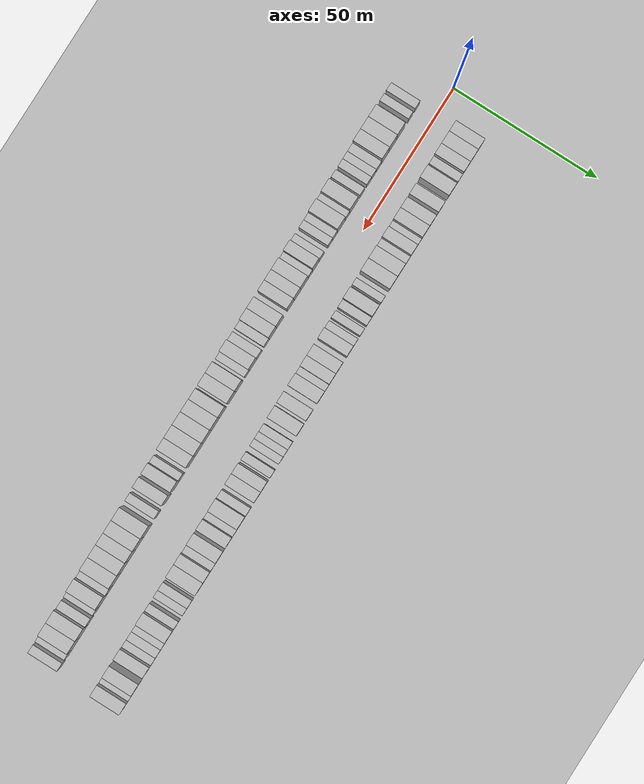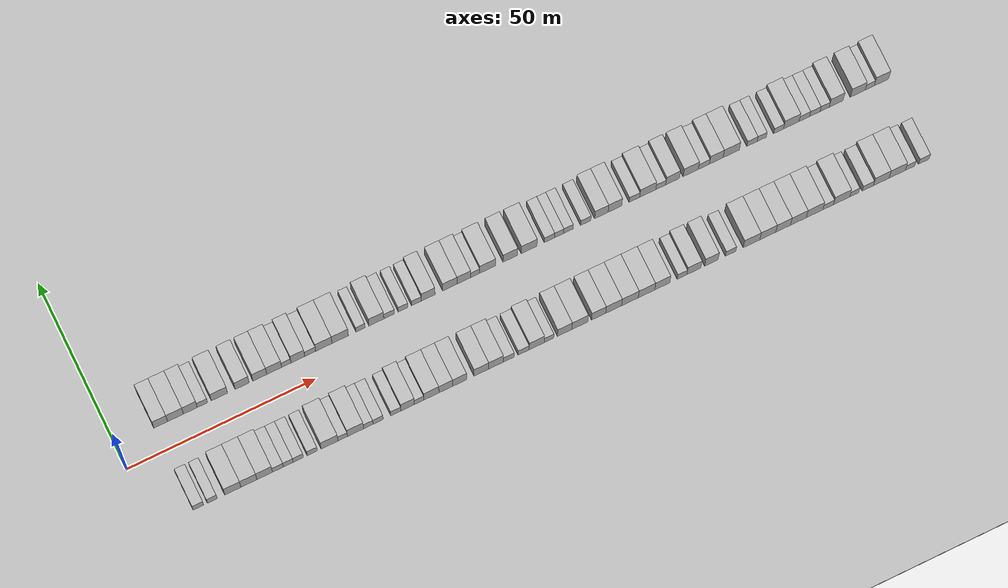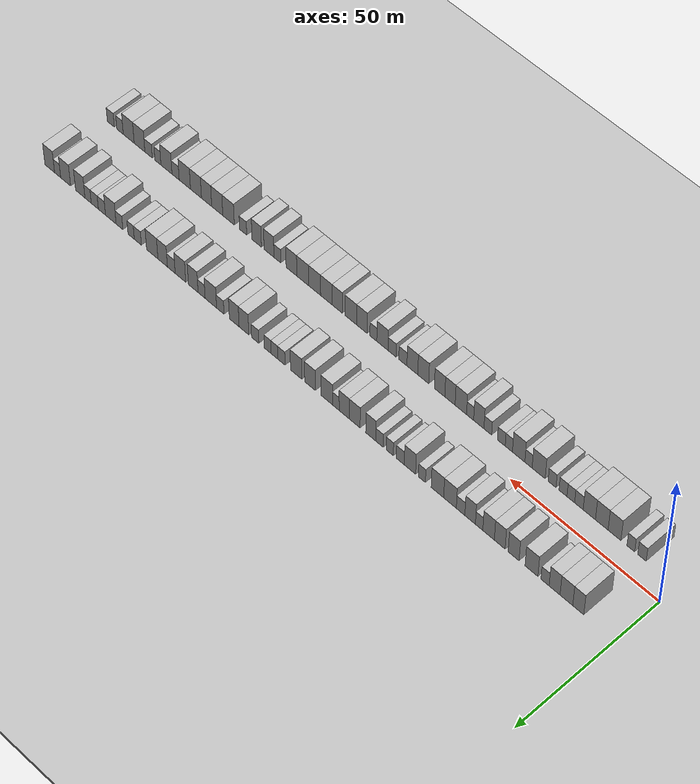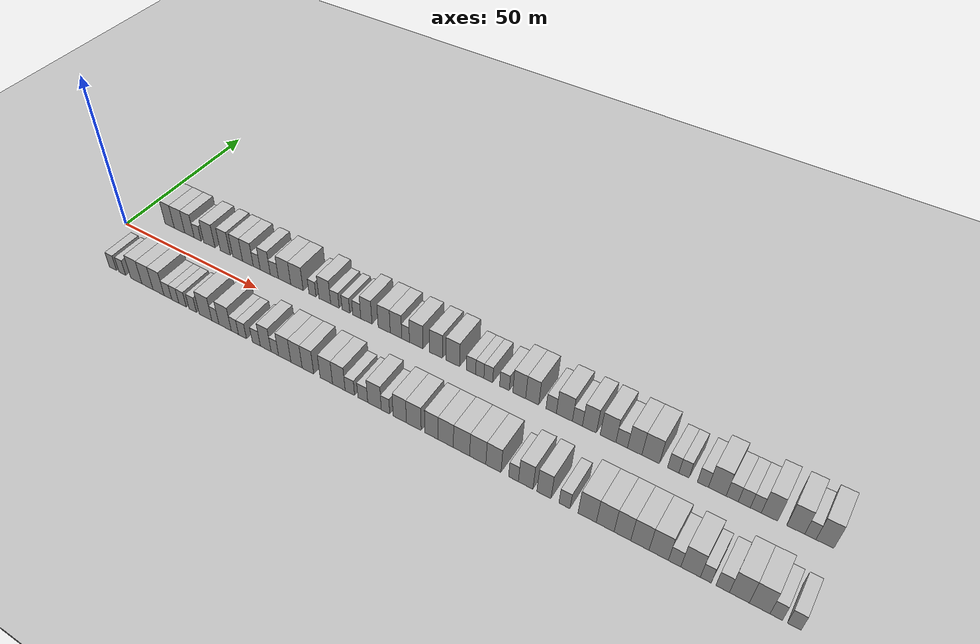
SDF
<?xml version="1.0" encoding="utf-8"?>

<sdf version="1.6">

   <world name="default">

      <gui fullscreen="0">

         <camera name="user_camera">

            <pose>-15 0 4.57585 0 0 0</pose>

            <view_controller>orbit</view_controller>

         </camera>

      </gui>

      <scene>

         <sky>

           <clouds>

             <speed>12</speed>

           </clouds>

         </sky>

         <ambient>0.4 0.4 0.4 1</ambient>

         <background>0.7 0.7 0.7 1</background>

         <shadows>1</shadows>

      </scene>

      <gravity>0 0 -9.8066</gravity>

      <magnetic_field>6e-06 2.3e-05 -4.2e-05</magnetic_field>

      <physics default="0" name="default_physics" type="ode">

         <ode>

            <solver>

               <type>quick</type>

               <iters>10</iters>

               <sor>1.0</sor>

               <use_dynamic_moi_rescaling>0</use_dynamic_moi_rescaling>

            </solver>

            <constraints>

               <cfm>0</cfm>

               <erp>0.2</erp>

               <contact_max_correcting_vel>100</contact_max_correcting_vel>

               <contact_surface_layer>0.001</contact_surface_layer>

            </constraints>

         </ode>

         <max_step_size>0.004</max_step_size>

         <real_time_factor>1</real_time_factor>

         <real_time_update_rate>250</real_time_update_rate>

      </physics>

      <light name="sun" type="directional">

         <cast_shadows>1</cast_shadows>

         <pose>0 0 10 0 0 0</pose>

         <diffuse>0.8 0.8 0.8 1</diffuse>

         <specular>0.2 0.2 0.2 1</specular>

         <attenuation>

            <range>1000</range>

            <constant>0.9</constant>

            <linear>0.01</linear>

            <quadratic>0.001</quadratic>

         </attenuation>

         <direction>-0.5 0.1 -0.9</direction>

      </light>

      <include>

         <name>ground_plane_1</name>

         <uri>model://HANNAS_ground_plane</uri>

         <pose>0 0 0  0 0 0</pose>

      </include>

      <include>

         <name>ground_plane_2</name>

         <uri>model://HANNAS_ground_plane</uri>

         <pose>100 0 0  0 0 0</pose>

      </include>

      <model name="building_1">

         <static>1</static>

         <pose frame="">11.8167 11.0000 0 0.000000 0.000000 1.570796</pose>

         <link name="link">

            <pose frame="">0 0 4.50 0 0 0</pose>

            <collision name="collision">

               <geometry>

                  <box>

                     <size>10.0000 3.6334 9.0000</size>

                  </box>

               </geometry>

               <max_contacts>10</max_contacts>

               <surface>

                  <contact>

                     <ode/>

                  </contact>

                  <bounce/>

                  <friction>

                     <torsional>

                        <ode/>

                     </torsional>

                     <ode/>

                  </friction>

               </surface>

            </collision>

            <visual name="visual">

               <cast_shadows>0</cast_shadows>

               <geometry>

                  <box>

                     <size>10.0000 3.6334 9.0000</size>

                  </box>

               </geometry>

               <material>

                  <script>

                     <uri>model://HANNAS_wall/materials/scripts</uri>

                     <uri>model://HANNAS_wall/materials/textures</uri>

                     <name>vrc/HANNAS_wall</name>

                  </script>

               </material>

            </visual>

            <self_collide>0</self_collide>

            <enable_wind>0</enable_wind>

            <kinematic>0</kinematic>

         </link>

      </model>

      <model name="building_2">

         <static>1</static>

         <pose frame="">15.7360 11.0000 0 0.000000 0.000000 1.570796</pose>

         <link name="link">

            <pose frame="">0 0 4.50 0 0 0</pose>

            <collision name="collision">

               <geometry>

                  <box>

                     <size>10.0000 4.2052 9.0000</size>

                  </box>

               </geometry>

               <max_contacts>10</max_contacts>

               <surface>

                  <contact>

                     <ode/>

                  </contact>

                  <bounce/>

                  <friction>

                     <torsional>

                        <ode/>

                     </torsional>

                     <ode/>

                  </friction>

               </surface>

            </collision>

            <visual name="visual">

               <cast_shadows>0</cast_shadows>

               <geometry>

                  <box>

                     <size>10.0000 4.2052 9.0000</size>

                  </box>

               </geometry>

               <material>

                  <script>

                     <uri>model://HANNAS_wall/materials/scripts</uri>

                     <uri>model://HANNAS_wall/materials/textures</uri>

                     <name>vrc/HANNAS_wall</name>

                  </script>

               </material>

            </visual>

            <self_collide>0</self_collide>

            <enable_wind>0</enable_wind>

            <kinematic>0</kinematic>

         </link>

      </model>

      <model name="building_3">

         <static>1</static>

         <pose frame="">19.6542 11.0000 0 0.000000 0.000000 1.570796</pose>

         <link name="link">

            <pose frame="">0 0 4.50 0 0 0</pose>

            <collision name="collision">

               <geometry>

                  <box>

                     <size>10.0000 3.6313 9.0000</size>

                  </box>

               </geometry>

               <max_contacts>10</max_contacts>

               <surface>

                  <contact>

                     <ode/>

                  </contact>

                  <bounce/>

                  <friction>

                     <torsional>

                        <ode/>

                     </torsional>

                     <ode/>

                  </friction>

               </surface>

            </collision>

            <visual name="visual">

               <cast_shadows>0</cast_shadows>

               <geometry>

                  <box>

                     <size>10.0000 3.6313 9.0000</size>

                  </box>

               </geometry>

               <material>

                  <script>

                     <uri>model://HANNAS_wall/materials/scripts</uri>

                     <uri>model://HANNAS_wall/materials/textures</uri>

                     <name>vrc/HANNAS_wall</name>

                  </script>

               </material>

            </visual>

            <self_collide>0</self_collide>

            <enable_wind>0</enable_wind>

            <kinematic>0</kinematic>

         </link>

      </model>

      <model name="building_4">

         <static>1</static>

         <pose frame="">22.8331 11.0000 0 0.000000 0.000000 1.570796</pose>

         <link name="link">

            <pose frame="">0 0 3.00 0 0 0</pose>

            <collision name="collision">

               <geometry>

                  <box>

                     <size>10.0000 2.7264 6.0000</size>

                  </box>

               </geometry>

               <max_contacts>10</max_contacts>

               <surface>

                  <contact>

                     <ode/>

                  </contact>

                  <bounce/>

                  <friction>

                     <torsional>

                        <ode/>

                     </torsional>

                     <ode/>

                  </friction>

               </surface>

            </collision>

            <visual name="visual">

               <cast_shadows>0</cast_shadows>

               <geometry>

                  <box>

                     <size>10.0000 2.7264 6.0000</size>

                  </box>

               </geometry>

               <material>

                  <script>

                     <uri>model://HANNAS_wall/materials/scripts</uri>

                     <uri>model://HANNAS_wall/materials/textures</uri>

                     <name>vrc/HANNAS_wall</name>

                  </script>

               </material>

            </visual>

            <self_collide>0</self_collide>

            <enable_wind>0</enable_wind>

            <kinematic>0</kinematic>

         </link>

      </model>

      <model name="building_5">

         <static>1</static>

         <pose frame="">27.3559 11.0000 0 0.000000 0.000000 1.570796</pose>

         <link name="link">

            <pose frame="">0 0 4.50 0 0 0</pose>

            <collision name="collision">

               <geometry>

                  <box>

                     <size>10.0000 4.3192 9.0000</size>

                  </box>

               </geometry>

               <max_contacts>10</max_contacts>

               <surface>

                  <contact>

                     <ode/>

                  </contact>

                  <bounce/>

                  <friction>

                     <torsional>

                        <ode/>

                     </torsional>

                     <ode/>

                  </friction>

               </surface>

            </collision>

            <visual name="visual">

               <cast_shadows>0</cast_shadows>

               <geometry>

                  <box>

                     <size>10.0000 4.3192 9.0000</size>

                  </box>

               </geometry>

               <material>

                  <script>

                     <uri>model://HANNAS_wall/materials/scripts</uri>

                     <uri>model://HANNAS_wall/materials/textures</uri>

                     <name>vrc/HANNAS_wall</name>

                  </script>

               </material>

            </visual>

            <self_collide>0</self_collide>

            <enable_wind>0</enable_wind>

            <kinematic>0</kinematic>

         </link>

      </model>

      <model name="building_6">

         <static>1</static>

         <pose frame="">33.3677 11.0000 0 0.000000 0.000000 1.570796</pose>

         <link name="link">

            <pose frame="">0 0 4.50 0 0 0</pose>

            <collision name="collision">

               <geometry>

                  <box>

                     <size>10.0000 3.7043 9.0000</size>

                  </box>

               </geometry>

               <max_contacts>10</max_contacts>

               <surface>

                  <contact>

                     <ode/>

                  </contact>

                  <bounce/>

                  <friction>

                     <torsional>

                        <ode/>

                     </torsional>

                     <ode/>

                  </friction>

               </surface>

            </collision>

            <visual name="visual">

               <cast_shadows>0</cast_shadows>

               <geometry>

                  <box>

                     <size>10.0000 3.7043 9.0000</size>

                  </box>

               </geometry>

               <material>

                  <script>

                     <uri>model://HANNAS_wall/materials/scripts</uri>

                     <uri>model://HANNAS_wall/materials/textures</uri>

                     <name>vrc/HANNAS_wall</name>

                  </script>

               </material>

            </visual>

            <self_collide>0</self_collide>

            <enable_wind>0</enable_wind>

            <kinematic>0</kinematic>

         </link>

      </model>

      <model name="building_7">

         <static>1</static>

         <pose frame="">38.0490 11.0000 0 0.000000 0.000000 1.570796</pose>

         <link name="link">

            <pose frame="">0 0 4.50 0 0 0</pose>

            <collision name="collision">

               <geometry>

                  <box>

                     <size>10.0000 3.6584 9.0000</size>

                  </box>

               </geometry>

               <max_contacts>10</max_contacts>

               <surface>

                  <contact>

                     <ode/>

                  </contact>

                  <bounce/>

                  <friction>

                     <torsional>

                        <ode/>

                     </torsional>

                     <ode/>

                  </friction>

               </surface>

            </collision>

            <visual name="visual">

               <cast_shadows>0</cast_shadows>

               <geometry>

                  <box>

                     <size>10.0000 3.6584 9.0000</size>

                  </box>

               </geometry>

               <material>

                  <script>

                     <uri>model://HANNAS_wall/materials/scripts</uri>

                     <uri>model://HANNAS_wall/materials/textures</uri>

                     <name>vrc/HANNAS_wall</name>

                  </script>

               </material>

            </visual>

            <self_collide>0</self_collide>

            <enable_wind>0</enable_wind>

            <kinematic>0</kinematic>

         </link>

      </model>

      <model name="building_8">

         <static>1</static>

         <pose frame="">41.8445 11.0000 0 0.000000 0.000000 1.570796</pose>

         <link name="link">

            <pose frame="">0 0 4.50 0 0 0</pose>

            <collision name="collision">

               <geometry>

                  <box>

                     <size>10.0000 3.9326 9.0000</size>

                  </box>

               </geometry>

               <max_contacts>10</max_contacts>

               <surface>

                  <contact>

                     <ode/>

                  </contact>

                  <bounce/>

                  <friction>

                     <torsional>

                        <ode/>

                     </torsional>

                     <ode/>

                  </friction>

               </surface>

            </collision>

            <visual name="visual">

               <cast_shadows>0</cast_shadows>

               <geometry>

                  <box>

                     <size>10.0000 3.9326 9.0000</size>

                  </box>

               </geometry>

               <material>

                  <script>

                     <uri>model://HANNAS_wall/materials/scripts</uri>

                     <uri>model://HANNAS_wall/materials/textures</uri>

                     <name>vrc/HANNAS_wall</name>

                  </script>

               </material>

            </visual>

            <self_collide>0</self_collide>

            <enable_wind>0</enable_wind>

            <kinematic>0</kinematic>

         </link>

      </model>

      <model name="building_9">

         <static>1</static>

         <pose frame="">45.0715 11.0000 0 0.000000 0.000000 1.570796</pose>

         <link name="link">

            <pose frame="">0 0 3.00 0 0 0</pose>

            <collision name="collision">

               <geometry>

                  <box>

                     <size>10.0000 2.5213 6.0000</size>

                  </box>

               </geometry>

               <max_contacts>10</max_contacts>

               <surface>

                  <contact>

                     <ode/>

                  </contact>

                  <bounce/>

                  <friction>

                     <torsional>

                        <ode/>

                     </torsional>

                     <ode/>

                  </friction>

               </surface>

            </collision>

            <visual name="visual">

               <cast_shadows>0</cast_shadows>

               <geometry>

                  <box>

                     <size>10.0000 2.5213 6.0000</size>

                  </box>

               </geometry>

               <material>

                  <script>

                     <uri>model://HANNAS_wall/materials/scripts</uri>

                     <uri>model://HANNAS_wall/materials/textures</uri>

                     <name>vrc/HANNAS_wall</name>

                  </script>

               </material>

            </visual>

            <self_collide>0</self_collide>

            <enable_wind>0</enable_wind>

            <kinematic>0</kinematic>

         </link>

      </model>

      <model name="building_10">

         <static>1</static>

         <pose frame="">48.1417 11.0000 0 0.000000 0.000000 1.570796</pose>

         <link name="link">

            <pose frame="">0 0 4.50 0 0 0</pose>

            <collision name="collision">

               <geometry>

                  <box>

                     <size>10.0000 3.6191 9.0000</size>

                  </box>

               </geometry>

               <max_contacts>10</max_contacts>

               <surface>

                  <contact>

                     <ode/>

                  </contact>

                  <bounce/>

                  <friction>

                     <torsional>

                        <ode/>

                     </torsional>

                     <ode/>

                  </friction>

               </surface>

            </collision>

            <visual name="visual">

               <cast_shadows>0</cast_shadows>

               <geometry>

                  <box>

                     <size>10.0000 3.6191 9.0000</size>

                  </box>

               </geometry>

               <material>

                  <script>

                     <uri>model://HANNAS_wall/materials/scripts</uri>

                     <uri>model://HANNAS_wall/materials/textures</uri>

                     <name>vrc/HANNAS_wall</name>

                  </script>

               </material>

            </visual>

            <self_collide>0</self_collide>

            <enable_wind>0</enable_wind>

            <kinematic>0</kinematic>

         </link>

      </model>

      <model name="building_11">

         <static>1</static>

         <pose frame="">51.4159 11.0000 0 0.000000 0.000000 1.570796</pose>

         <link name="link">

            <pose frame="">0 0 3.00 0 0 0</pose>

            <collision name="collision">

               <geometry>

                  <box>

                     <size>10.0000 2.9294 6.0000</size>

                  </box>

               </geometry>

               <max_contacts>10</max_contacts>

               <surface>

                  <contact>

                     <ode/>

                  </contact>

                  <bounce/>

                  <friction>

                     <torsional>

                        <ode/>

                     </torsional>

                     <ode/>

                  </friction>

               </surface>

            </collision>

            <visual name="visual">

               <cast_shadows>0</cast_shadows>

               <geometry>

                  <box>

                     <size>10.0000 2.9294 6.0000</size>

                  </box>

               </geometry>

               <material>

                  <script>

                     <uri>model://HANNAS_wall/materials/scripts</uri>

                     <uri>model://HANNAS_wall/materials/textures</uri>

                     <name>vrc/HANNAS_wall</name>

                  </script>

               </material>

            </visual>

            <self_collide>0</self_collide>

            <enable_wind>0</enable_wind>

            <kinematic>0</kinematic>

         </link>

      </model>

      <model name="building_12">

         <static>1</static>

         <pose frame="">55.0609 11.0000 0 0.000000 0.000000 1.570796</pose>

         <link name="link">

            <pose frame="">0 0 4.50 0 0 0</pose>

            <collision name="collision">

               <geometry>

                  <box>

                     <size>10.0000 4.3606 9.0000</size>

                  </box>

               </geometry>

               <max_contacts>10</max_contacts>

               <surface>

                  <contact>

                     <ode/>

                  </contact>

                  <bounce/>

                  <friction>

                     <torsional>

                        <ode/>

                     </torsional>

                     <ode/>

                  </friction>

               </surface>

            </collision>

            <visual name="visual">

               <cast_shadows>0</cast_shadows>

               <geometry>

                  <box>

                     <size>10.0000 4.3606 9.0000</size>

                  </box>

               </geometry>

               <material>

                  <script>

                     <uri>model://HANNAS_wall/materials/scripts</uri>

                     <uri>model://HANNAS_wall/materials/textures</uri>

                     <name>vrc/HANNAS_wall</name>

                  </script>

               </material>

            </visual>

            <self_collide>0</self_collide>

            <enable_wind>0</enable_wind>

            <kinematic>0</kinematic>

         </link>

      </model>

      <model name="building_13">

         <static>1</static>

         <pose frame="">59.4143 11.0000 0 0.000000 0.000000 1.570796</pose>

         <link name="link">

            <pose frame="">0 0 4.50 0 0 0</pose>

            <collision name="collision">

               <geometry>

                  <box>

                     <size>10.0000 4.3462 9.0000</size>

                  </box>

               </geometry>

               <max_contacts>10</max_contacts>

               <surface>

                  <contact>

                     <ode/>

                  </contact>

                  <bounce/>

                  <friction>

                     <torsional>

                        <ode/>

                     </torsional>

                     <ode/>

                  </friction>

               </surface>

            </collision>

            <visual name="visual">

               <cast_shadows>0</cast_shadows>

               <geometry>

                  <box>

                     <size>10.0000 4.3462 9.0000</size>

                  </box>

               </geometry>

               <material>

                  <script>

                     <uri>model://HANNAS_wall/materials/scripts</uri>

                     <uri>model://HANNAS_wall/materials/textures</uri>

                     <name>vrc/HANNAS_wall</name>

                  </script>

               </material>

            </visual>

            <self_collide>0</self_collide>

            <enable_wind>0</enable_wind>

            <kinematic>0</kinematic>

         </link>

      </model>

      <model name="building_14">

         <static>1</static>

         <pose frame="">64.8036 11.0000 0 0.000000 0.000000 1.570796</pose>

         <link name="link">

            <pose frame="">0 0 3.00 0 0 0</pose>

            <collision name="collision">

               <geometry>

                  <box>

                     <size>10.0000 2.4323 6.0000</size>

                  </box>

               </geometry>

               <max_contacts>10</max_contacts>

               <surface>

                  <contact>

                     <ode/>

                  </contact>

                  <bounce/>

                  <friction>

                     <torsional>

                        <ode/>

                     </torsional>

                     <ode/>

                  </friction>

               </surface>

            </collision>

            <visual name="visual">

               <cast_shadows>0</cast_shadows>

               <geometry>

                  <box>

                     <size>10.0000 2.4323 6.0000</size>

                  </box>

               </geometry>

               <material>

                  <script>

                     <uri>model://HANNAS_wall/materials/scripts</uri>

                     <uri>model://HANNAS_wall/materials/textures</uri>

                     <name>vrc/HANNAS_wall</name>

                  </script>

               </material>

            </visual>

            <self_collide>0</self_collide>

            <enable_wind>0</enable_wind>

            <kinematic>0</kinematic>

         </link>

      </model>

      <model name="building_15">

         <static>1</static>

         <pose frame="">69.0086 11.0000 0 0.000000 0.000000 1.570796</pose>

         <link name="link">

            <pose frame="">0 0 4.50 0 0 0</pose>

            <collision name="collision">

               <geometry>

                  <box>

                     <size>10.0000 3.9777 9.0000</size>

                  </box>

               </geometry>

               <max_contacts>10</max_contacts>

               <surface>

                  <contact>

                     <ode/>

                  </contact>

                  <bounce/>

                  <friction>

                     <torsional>

                        <ode/>

                     </torsional>

                     <ode/>

                  </friction>

               </surface>

            </collision>

            <visual name="visual">

               <cast_shadows>0</cast_shadows>

               <geometry>

                  <box>

                     <size>10.0000 3.9777 9.0000</size>

                  </box>

               </geometry>

               <material>

                  <script>

                     <uri>model://HANNAS_wall/materials/scripts</uri>

                     <uri>model://HANNAS_wall/materials/textures</uri>

                     <name>vrc/HANNAS_wall</name>

                  </script>

               </material>

            </visual>

            <self_collide>0</self_collide>

            <enable_wind>0</enable_wind>

            <kinematic>0</kinematic>

         </link>

      </model>

      <model name="building_16">

         <static>1</static>

         <pose frame="">72.4203 11.0000 0 0.000000 0.000000 1.570796</pose>

         <link name="link">

            <pose frame="">0 0 3.00 0 0 0</pose>

            <collision name="collision">

               <geometry>

                  <box>

                     <size>10.0000 2.8458 6.0000</size>

                  </box>

               </geometry>

               <max_contacts>10</max_contacts>

               <surface>

                  <contact>

                     <ode/>

                  </contact>

                  <bounce/>

                  <friction>

                     <torsional>

                        <ode/>

                     </torsional>

                     <ode/>

                  </friction>

               </surface>

            </collision>

            <visual name="visual">

               <cast_shadows>0</cast_shadows>

               <geometry>

                  <box>

                     <size>10.0000 2.8458 6.0000</size>

                  </box>

               </geometry>

               <material>

                  <script>

                     <uri>model://HANNAS_wall/materials/scripts</uri>

                     <uri>model://HANNAS_wall/materials/textures</uri>

                     <name>vrc/HANNAS_wall</name>

                  </script>

               </material>

            </visual>

            <self_collide>0</self_collide>

            <enable_wind>0</enable_wind>

            <kinematic>0</kinematic>

         </link>

      </model>

      <model name="building_17">

         <static>1</static>

         <pose frame="">76.1147 11.0000 0 0.000000 0.000000 1.570796</pose>

         <link name="link">

            <pose frame="">0 0 3.00 0 0 0</pose>

            <collision name="collision">

               <geometry>

                  <box>

                     <size>10.0000 2.5430 6.0000</size>

                  </box>

               </geometry>

               <max_contacts>10</max_contacts>

               <surface>

                  <contact>

                     <ode/>

                  </contact>

                  <bounce/>

                  <friction>

                     <torsional>

                        <ode/>

                     </torsional>

                     <ode/>

                  </friction>

               </surface>

            </collision>

            <visual name="visual">

               <cast_shadows>0</cast_shadows>

               <geometry>

                  <box>

                     <size>10.0000 2.5430 6.0000</size>

                  </box>

               </geometry>

               <material>

                  <script>

                     <uri>model://HANNAS_wall/materials/scripts</uri>

                     <uri>model://HANNAS_wall/materials/textures</uri>

                     <name>vrc/HANNAS_wall</name>

                  </script>

               </material>

            </visual>

            <self_collide>0</self_collide>

            <enable_wind>0</enable_wind>

            <kinematic>0</kinematic>

         </link>

      </model>

      <model name="building_18">

         <static>1</static>

         <pose frame="">79.7044 11.0000 0 0.000000 0.000000 1.570796</pose>

         <link name="link">

            <pose frame="">0 0 3.00 0 0 0</pose>

            <collision name="collision">

               <geometry>

                  <box>

                     <size>10.0000 2.6365 6.0000</size>

                  </box>

               </geometry>

               <max_contacts>10</max_contacts>

               <surface>

                  <contact>

                     <ode/>

                  </contact>

                  <bounce/>

                  <friction>

                     <torsional>

                        <ode/>

                     </torsional>

                     <ode/>

                  </friction>

               </surface>

            </collision>

            <visual name="visual">

               <cast_shadows>0</cast_shadows>

               <geometry>

                  <box>

                     <size>10.0000 2.6365 6.0000</size>

                  </box>

               </geometry>

               <material>

                  <script>

                     <uri>model://HANNAS_wall/materials/scripts</uri>

                     <uri>model://HANNAS_wall/materials/textures</uri>

                     <name>vrc/HANNAS_wall</name>

                  </script>

               </material>

            </visual>

            <self_collide>0</self_collide>

            <enable_wind>0</enable_wind>

            <kinematic>0</kinematic>

         </link>

      </model>

      <model name="building_19">

         <static>1</static>

         <pose frame="">82.8372 11.0000 0 0.000000 0.000000 1.570796</pose>

         <link name="link">

            <pose frame="">0 0 4.50 0 0 0</pose>

            <collision name="collision">

               <geometry>

                  <box>

                     <size>10.0000 3.6291 9.0000</size>

                  </box>

               </geometry>

               <max_contacts>10</max_contacts>

               <surface>

                  <contact>

                     <ode/>

                  </contact>

                  <bounce/>

                  <friction>

                     <torsional>

                        <ode/>

                     </torsional>

                     <ode/>

                  </friction>

               </surface>

            </collision>

            <visual name="visual">

               <cast_shadows>0</cast_shadows>

               <geometry>

                  <box>

                     <size>10.0000 3.6291 9.0000</size>

                  </box>

               </geometry>

               <material>

                  <script>

                     <uri>model://HANNAS_wall/materials/scripts</uri>

                     <uri>model://HANNAS_wall/materials/textures</uri>

                     <name>vrc/HANNAS_wall</name>

                  </script>

               </material>

            </visual>

            <self_collide>0</self_collide>

            <enable_wind>0</enable_wind>

            <kinematic>0</kinematic>

         </link>

      </model>

      <model name="building_20">

         <static>1</static>

         <pose frame="">88.5892 11.0000 0 0.000000 0.000000 1.570796</pose>

         <link name="link">

            <pose frame="">0 0 4.50 0 0 0</pose>

            <collision name="collision">

               <geometry>

                  <box>

                     <size>10.0000 3.8748 9.0000</size>

                  </box>

               </geometry>

               <max_contacts>10</max_contacts>

               <surface>

                  <contact>

                     <ode/>

                  </contact>

                  <bounce/>

                  <friction>

                     <torsional>

                        <ode/>

                     </torsional>

                     <ode/>

                  </friction>

               </surface>

            </collision>

            <visual name="visual">

               <cast_shadows>0</cast_shadows>

               <geometry>

                  <box>

                     <size>10.0000 3.8748 9.0000</size>

                  </box>

               </geometry>

               <material>

                  <script>

                     <uri>model://HANNAS_wall/materials/scripts</uri>

                     <uri>model://HANNAS_wall/materials/textures</uri>

                     <name>vrc/HANNAS_wall</name>

                  </script>

               </material>

            </visual>

            <self_collide>0</self_collide>

            <enable_wind>0</enable_wind>

            <kinematic>0</kinematic>

         </link>

      </model>

      <model name="building_21">

         <static>1</static>

         <pose frame="">92.3459 11.0000 0 0.000000 0.000000 1.570796</pose>

         <link name="link">

            <pose frame="">0 0 4.50 0 0 0</pose>

            <collision name="collision">

               <geometry>

                  <box>

                     <size>10.0000 3.6386 9.0000</size>

                  </box>

               </geometry>

               <max_contacts>10</max_contacts>

               <surface>

                  <contact>

                     <ode/>

                  </contact>

                  <bounce/>

                  <friction>

                     <torsional>

                        <ode/>

                     </torsional>

                     <ode/>

                  </friction>

               </surface>

            </collision>

            <visual name="visual">

               <cast_shadows>0</cast_shadows>

               <geometry>

                  <box>

                     <size>10.0000 3.6386 9.0000</size>

                  </box>

               </geometry>

               <material>

                  <script>

                     <uri>model://HANNAS_wall/materials/scripts</uri>

                     <uri>model://HANNAS_wall/materials/textures</uri>

                     <name>vrc/HANNAS_wall</name>

                  </script>

               </material>

            </visual>

            <self_collide>0</self_collide>

            <enable_wind>0</enable_wind>

            <kinematic>0</kinematic>

         </link>

      </model>

      <model name="building_22">

         <static>1</static>

         <pose frame="">95.3682 11.0000 0 0.000000 0.000000 1.570796</pose>

         <link name="link">

            <pose frame="">0 0 3.00 0 0 0</pose>

            <collision name="collision">

               <geometry>

                  <box>

                     <size>10.0000 2.4060 6.0000</size>

                  </box>

               </geometry>

               <max_contacts>10</max_contacts>

               <surface>

                  <contact>

                     <ode/>

                  </contact>

                  <bounce/>

                  <friction>

                     <torsional>

                        <ode/>

                     </torsional>

                     <ode/>

                  </friction>

               </surface>

            </collision>

            <visual name="visual">

               <cast_shadows>0</cast_shadows>

               <geometry>

                  <box>

                     <size>10.0000 2.4060 6.0000</size>

                  </box>

               </geometry>

               <material>

                  <script>

                     <uri>model://HANNAS_wall/materials/scripts</uri>

                     <uri>model://HANNAS_wall/materials/textures</uri>

                     <name>vrc/HANNAS_wall</name>

                  </script>

               </material>

            </visual>

            <self_collide>0</self_collide>

            <enable_wind>0</enable_wind>

            <kinematic>0</kinematic>

         </link>

      </model>

      <model name="building_23">

         <static>1</static>

         <pose frame="">98.6794 11.0000 0 0.000000 0.000000 1.570796</pose>

         <link name="link">

            <pose frame="">0 0 4.50 0 0 0</pose>

            <collision name="collision">

               <geometry>

                  <box>

                     <size>10.0000 4.2166 9.0000</size>

                  </box>

               </geometry>

               <max_contacts>10</max_contacts>

               <surface>

                  <contact>

                     <ode/>

                  </contact>

                  <bounce/>

                  <friction>

                     <torsional>

                        <ode/>

                     </torsional>

                     <ode/>

                  </friction>

               </surface>

            </collision>

            <visual name="visual">

               <cast_shadows>0</cast_shadows>

               <geometry>

                  <box>

                     <size>10.0000 4.2166 9.0000</size>

                  </box>

               </geometry>

               <material>

                  <script>

                     <uri>model://HANNAS_wall/materials/scripts</uri>

                     <uri>model://HANNAS_wall/materials/textures</uri>

                     <name>vrc/HANNAS_wall</name>

                  </script>

               </material>

            </visual>

            <self_collide>0</self_collide>

            <enable_wind>0</enable_wind>

            <kinematic>0</kinematic>

         </link>

      </model>

      <model name="building_24">

         <static>1</static>

         <pose frame="">104.7415 11.0000 0 0.000000 0.000000 1.570796</pose>

         <link name="link">

            <pose frame="">0 0 4.50 0 0 0</pose>

            <collision name="collision">

               <geometry>

                  <box>

                     <size>10.0000 3.9074 9.0000</size>

                  </box>

               </geometry>

               <max_contacts>10</max_contacts>

               <surface>

                  <contact>

                     <ode/>

                  </contact>

                  <bounce/>

                  <friction>

                     <torsional>

                        <ode/>

                     </torsional>

                     <ode/>

                  </friction>

               </surface>

            </collision>

            <visual name="visual">

               <cast_shadows>0</cast_shadows>

               <geometry>

                  <box>

                     <size>10.0000 3.9074 9.0000</size>

                  </box>

               </geometry>

               <material>

                  <script>

                     <uri>model://HANNAS_wall/materials/scripts</uri>

                     <uri>model://HANNAS_wall/materials/textures</uri>

                     <name>vrc/HANNAS_wall</name>

                  </script>

               </material>

            </visual>

            <self_collide>0</self_collide>

            <enable_wind>0</enable_wind>

            <kinematic>0</kinematic>

         </link>

      </model>

      <model name="building_25">

         <static>1</static>

         <pose frame="">109.7811 11.0000 0 0.000000 0.000000 1.570796</pose>

         <link name="link">

            <pose frame="">0 0 4.50 0 0 0</pose>

            <collision name="collision">

               <geometry>

                  <box>

                     <size>10.0000 4.1719 9.0000</size>

                  </box>

               </geometry>

               <max_contacts>10</max_contacts>

               <surface>

                  <contact>

                     <ode/>

                  </contact>

                  <bounce/>

                  <friction>

                     <torsional>

                        <ode/>

                     </torsional>

                     <ode/>

                  </friction>

               </surface>

            </collision>

            <visual name="visual">

               <cast_shadows>0</cast_shadows>

               <geometry>

                  <box>

                     <size>10.0000 4.1719 9.0000</size>

                  </box>

               </geometry>

               <material>

                  <script>

                     <uri>model://HANNAS_wall/materials/scripts</uri>

                     <uri>model://HANNAS_wall/materials/textures</uri>

                     <name>vrc/HANNAS_wall</name>

                  </script>

               </material>

            </visual>

            <self_collide>0</self_collide>

            <enable_wind>0</enable_wind>

            <kinematic>0</kinematic>

         </link>

      </model>

      <model name="building_26">

         <static>1</static>

         <pose frame="">115.2230 11.0000 0 0.000000 0.000000 1.570796</pose>

         <link name="link">

            <pose frame="">0 0 3.00 0 0 0</pose>

            <collision name="collision">

               <geometry>

                  <box>

                     <size>10.0000 2.7119 6.0000</size>

                  </box>

               </geometry>

               <max_contacts>10</max_contacts>

               <surface>

                  <contact>

                     <ode/>

                  </contact>

                  <bounce/>

                  <friction>

                     <torsional>

                        <ode/>

                     </torsional>

                     <ode/>

                  </friction>

               </surface>

            </collision>

            <visual name="visual">

               <cast_shadows>0</cast_shadows>

               <geometry>

                  <box>

                     <size>10.0000 2.7119 6.0000</size>

                  </box>

               </geometry>

               <material>

                  <script>

                     <uri>model://HANNAS_wall/materials/scripts</uri>

                     <uri>model://HANNAS_wall/materials/textures</uri>

                     <name>vrc/HANNAS_wall</name>

                  </script>

               </material>

            </visual>

            <self_collide>0</self_collide>

            <enable_wind>0</enable_wind>

            <kinematic>0</kinematic>

         </link>

      </model>

      <model name="building_27">

         <static>1</static>

         <pose frame="">117.8030 11.0000 0 0.000000 0.000000 1.570796</pose>

         <link name="link">

            <pose frame="">0 0 3.00 0 0 0</pose>

            <collision name="collision">

               <geometry>

                  <box>

                     <size>10.0000 2.4482 6.0000</size>

                  </box>

               </geometry>

               <max_contacts>10</max_contacts>

               <surface>

                  <contact>

                     <ode/>

                  </contact>

                  <bounce/>

                  <friction>

                     <torsional>

                        <ode/>

                     </torsional>

                     <ode/>

                  </friction>

               </surface>

            </collision>

            <visual name="visual">

               <cast_shadows>0</cast_shadows>

               <geometry>

                  <box>

                     <size>10.0000 2.4482 6.0000</size>

                  </box>

               </geometry>

               <material>

                  <script>

                     <uri>model://HANNAS_wall/materials/scripts</uri>

                     <uri>model://HANNAS_wall/materials/textures</uri>

                     <name>vrc/HANNAS_wall</name>

                  </script>

               </material>

            </visual>

            <self_collide>0</self_collide>

            <enable_wind>0</enable_wind>

            <kinematic>0</kinematic>

         </link>

      </model>

      <model name="building_28">

         <static>1</static>

         <pose frame="">120.2904 11.0000 0 0.000000 0.000000 1.570796</pose>

         <link name="link">

            <pose frame="">0 0 3.00 0 0 0</pose>

            <collision name="collision">

               <geometry>

                  <box>

                     <size>10.0000 2.5265 6.0000</size>

                  </box>

               </geometry>

               <max_contacts>10</max_contacts>

               <surface>

                  <contact>

                     <ode/>

                  </contact>

                  <bounce/>

                  <friction>

                     <torsional>

                        <ode/>

                     </torsional>

                     <ode/>

                  </friction>

               </surface>

            </collision>

            <visual name="visual">

               <cast_shadows>0</cast_shadows>

               <geometry>

                  <box>

                     <size>10.0000 2.5265 6.0000</size>

                  </box>

               </geometry>

               <material>

                  <script>

                     <uri>model://HANNAS_wall/materials/scripts</uri>

                     <uri>model://HANNAS_wall/materials/textures</uri>

                     <name>vrc/HANNAS_wall</name>

                  </script>

               </material>

            </visual>

            <self_collide>0</self_collide>

            <enable_wind>0</enable_wind>

            <kinematic>0</kinematic>

         </link>

      </model>

      <model name="building_29">

         <static>1</static>

         <pose frame="">124.9317 11.0000 0 0.000000 0.000000 1.570796</pose>

         <link name="link">

            <pose frame="">0 0 3.00 0 0 0</pose>

            <collision name="collision">

               <geometry>

                  <box>

                     <size>10.0000 2.7562 6.0000</size>

                  </box>

               </geometry>

               <max_contacts>10</max_contacts>

               <surface>

                  <contact>

                     <ode/>

                  </contact>

                  <bounce/>

                  <friction>

                     <torsional>

                        <ode/>

                     </torsional>

                     <ode/>

                  </friction>

               </surface>

            </collision>

            <visual name="visual">

               <cast_shadows>0</cast_shadows>

               <geometry>

                  <box>

                     <size>10.0000 2.7562 6.0000</size>

                  </box>

               </geometry>

               <material>

                  <script>

                     <uri>model://HANNAS_wall/materials/scripts</uri>

                     <uri>model://HANNAS_wall/materials/textures</uri>

                     <name>vrc/HANNAS_wall</name>

                  </script>

               </material>

            </visual>

            <self_collide>0</self_collide>

            <enable_wind>0</enable_wind>

            <kinematic>0</kinematic>

         </link>

      </model>

      <model name="building_30">

         <static>1</static>

         <pose frame="">129.1264 11.0000 0 0.000000 0.000000 1.570796</pose>

         <link name="link">

            <pose frame="">0 0 4.50 0 0 0</pose>

            <collision name="collision">

               <geometry>

                  <box>

                     <size>10.0000 3.6332 9.0000</size>

                  </box>

               </geometry>

               <max_contacts>10</max_contacts>

               <surface>

                  <contact>

                     <ode/>

                  </contact>

                  <bounce/>

                  <friction>

                     <torsional>

                        <ode/>

                     </torsional>

                     <ode/>

                  </friction>

               </surface>

            </collision>

            <visual name="visual">

               <cast_shadows>0</cast_shadows>

               <geometry>

                  <box>

                     <size>10.0000 3.6332 9.0000</size>

                  </box>

               </geometry>

               <material>

                  <script>

                     <uri>model://HANNAS_wall/materials/scripts</uri>

                     <uri>model://HANNAS_wall/materials/textures</uri>

                     <name>vrc/HANNAS_wall</name>

                  </script>

               </material>

            </visual>

            <self_collide>0</self_collide>

            <enable_wind>0</enable_wind>

            <kinematic>0</kinematic>

         </link>

      </model>

      <model name="building_31">

         <static>1</static>

         <pose frame="">132.7680 11.0000 0 0.000000 0.000000 1.570796</pose>

         <link name="link">

            <pose frame="">0 0 4.50 0 0 0</pose>

            <collision name="collision">

               <geometry>

                  <box>

                     <size>10.0000 3.6501 9.0000</size>

                  </box>

               </geometry>

               <max_contacts>10</max_contacts>

               <surface>

                  <contact>

                     <ode/>

                  </contact>

                  <bounce/>

                  <friction>

                     <torsional>

                        <ode/>

                     </torsional>

                     <ode/>

                  </friction>

               </surface>

            </collision>

            <visual name="visual">

               <cast_shadows>0</cast_shadows>

               <geometry>

                  <box>

                     <size>10.0000 3.6501 9.0000</size>

                  </box>

               </geometry>

               <material>

                  <script>

                     <uri>model://HANNAS_wall/materials/scripts</uri>

                     <uri>model://HANNAS_wall/materials/textures</uri>

                     <name>vrc/HANNAS_wall</name>

                  </script>

               </material>

            </visual>

            <self_collide>0</self_collide>

            <enable_wind>0</enable_wind>

            <kinematic>0</kinematic>

         </link>

      </model>

      <model name="building_32">

         <static>1</static>

         <pose frame="">138.0019 11.0000 0 0.000000 0.000000 1.570796</pose>

         <link name="link">

            <pose frame="">0 0 3.00 0 0 0</pose>

            <collision name="collision">

               <geometry>

                  <box>

                     <size>10.0000 2.8177 6.0000</size>

                  </box>

               </geometry>

               <max_contacts>10</max_contacts>

               <surface>

                  <contact>

                     <ode/>

                  </contact>

                  <bounce/>

                  <friction>

                     <torsional>

                        <ode/>

                     </torsional>

                     <ode/>

                  </friction>

               </surface>

            </collision>

            <visual name="visual">

               <cast_shadows>0</cast_shadows>

               <geometry>

                  <box>

                     <size>10.0000 2.8177 6.0000</size>

                  </box>

               </geometry>

               <material>

                  <script>

                     <uri>model://HANNAS_wall/materials/scripts</uri>

                     <uri>model://HANNAS_wall/materials/textures</uri>

                     <name>vrc/HANNAS_wall</name>

                  </script>

               </material>

            </visual>

            <self_collide>0</self_collide>

            <enable_wind>0</enable_wind>

            <kinematic>0</kinematic>

         </link>

      </model>

      <model name="building_33">

         <static>1</static>

         <pose frame="">141.5890 11.0000 0 0.000000 0.000000 1.570796</pose>

         <link name="link">

            <pose frame="">0 0 4.50 0 0 0</pose>

            <collision name="collision">

               <geometry>

                  <box>

                     <size>10.0000 4.3565 9.0000</size>

                  </box>

               </geometry>

               <max_contacts>10</max_contacts>

               <surface>

                  <contact>

                     <ode/>

                  </contact>

                  <bounce/>

                  <friction>

                     <torsional>

                        <ode/>

                     </torsional>

                     <ode/>

                  </friction>

               </surface>

            </collision>

            <visual name="visual">

               <cast_shadows>0</cast_shadows>

               <geometry>

                  <box>

                     <size>10.0000 4.3565 9.0000</size>

                  </box>

               </geometry>

               <material>

                  <script>

                     <uri>model://HANNAS_wall/materials/scripts</uri>

                     <uri>model://HANNAS_wall/materials/textures</uri>

                     <name>vrc/HANNAS_wall</name>

                  </script>

               </material>

            </visual>

            <self_collide>0</self_collide>

            <enable_wind>0</enable_wind>

            <kinematic>0</kinematic>

         </link>

      </model>

      <model name="building_34">

         <static>1</static>

         <pose frame="">145.1042 11.0000 0 0.000000 0.000000 1.570796</pose>

         <link name="link">

            <pose frame="">0 0 3.00 0 0 0</pose>

            <collision name="collision">

               <geometry>

                  <box>

                     <size>10.0000 2.6738 6.0000</size>

                  </box>

               </geometry>

               <max_contacts>10</max_contacts>

               <surface>

                  <contact>

                     <ode/>

                  </contact>

                  <bounce/>

                  <friction>

                     <torsional>

                        <ode/>

                     </torsional>

                     <ode/>

                  </friction>

               </surface>

            </collision>

            <visual name="visual">

               <cast_shadows>0</cast_shadows>

               <geometry>

                  <box>

                     <size>10.0000 2.6738 6.0000</size>

                  </box>

               </geometry>

               <material>

                  <script>

                     <uri>model://HANNAS_wall/materials/scripts</uri>

                     <uri>model://HANNAS_wall/materials/textures</uri>

                     <name>vrc/HANNAS_wall</name>

                  </script>

               </material>

            </visual>

            <self_collide>0</self_collide>

            <enable_wind>0</enable_wind>

            <kinematic>0</kinematic>

         </link>

      </model>

      <model name="building_35">

         <static>1</static>

         <pose frame="">148.2805 11.0000 0 0.000000 0.000000 1.570796</pose>

         <link name="link">

            <pose frame="">0 0 4.50 0 0 0</pose>

            <collision name="collision">

               <geometry>

                  <box>

                     <size>10.0000 3.6788 9.0000</size>

                  </box>

               </geometry>

               <max_contacts>10</max_contacts>

               <surface>

                  <contact>

                     <ode/>

                  </contact>

                  <bounce/>

                  <friction>

                     <torsional>

                        <ode/>

                     </torsional>

                     <ode/>

                  </friction>

               </surface>

            </collision>

            <visual name="visual">

               <cast_shadows>0</cast_shadows>

               <geometry>

                  <box>

                     <size>10.0000 3.6788 9.0000</size>

                  </box>

               </geometry>

               <material>

                  <script>

                     <uri>model://HANNAS_wall/materials/scripts</uri>

                     <uri>model://HANNAS_wall/materials/textures</uri>

                     <name>vrc/HANNAS_wall</name>

                  </script>

               </material>

            </visual>

            <self_collide>0</self_collide>

            <enable_wind>0</enable_wind>

            <kinematic>0</kinematic>

         </link>

      </model>

      <model name="building_36">

         <static>1</static>

         <pose frame="">153.1604 11.0000 0 0.000000 0.000000 1.570796</pose>

         <link name="link">

            <pose frame="">0 0 4.50 0 0 0</pose>

            <collision name="collision">

               <geometry>

                  <box>

                     <size>10.0000 4.0812 9.0000</size>

                  </box>

               </geometry>

               <max_contacts>10</max_contacts>

               <surface>

                  <contact>

                     <ode/>

                  </contact>

                  <bounce/>

                  <friction>

                     <torsional>

                        <ode/>

                     </torsional>

                     <ode/>

                  </friction>

               </surface>

            </collision>

            <visual name="visual">

               <cast_shadows>0</cast_shadows>

               <geometry>

                  <box>

                     <size>10.0000 4.0812 9.0000</size>

                  </box>

               </geometry>

               <material>

                  <script>

                     <uri>model://HANNAS_wall/materials/scripts</uri>

                     <uri>model://HANNAS_wall/materials/textures</uri>

                     <name>vrc/HANNAS_wall</name>

                  </script>

               </material>

            </visual>

            <self_collide>0</self_collide>

            <enable_wind>0</enable_wind>

            <kinematic>0</kinematic>

         </link>

      </model>

      <model name="building_37">

         <static>1</static>

         <pose frame="">156.6918 11.0000 0 0.000000 0.000000 1.570796</pose>

         <link name="link">

            <pose frame="">0 0 3.00 0 0 0</pose>

            <collision name="collision">

               <geometry>

                  <box>

                     <size>10.0000 2.9816 6.0000</size>

                  </box>

               </geometry>

               <max_contacts>10</max_contacts>

               <surface>

                  <contact>

                     <ode/>

                  </contact>

                  <bounce/>

                  <friction>

                     <torsional>

                        <ode/>

                     </torsional>

                     <ode/>

                  </friction>

               </surface>

            </collision>

            <visual name="visual">

               <cast_shadows>0</cast_shadows>

               <geometry>

                  <box>

                     <size>10.0000 2.9816 6.0000</size>

                  </box>

               </geometry>

               <material>

                  <script>

                     <uri>model://HANNAS_wall/materials/scripts</uri>

                     <uri>model://HANNAS_wall/materials/textures</uri>

                     <name>vrc/HANNAS_wall</name>

                  </script>

               </material>

            </visual>

            <self_collide>0</self_collide>

            <enable_wind>0</enable_wind>

            <kinematic>0</kinematic>

         </link>

      </model>

      <model name="building_38">

         <static>1</static>

         <pose frame="">160.0155 11.0000 0 0.000000 0.000000 1.570796</pose>

         <link name="link">

            <pose frame="">0 0 4.50 0 0 0</pose>

            <collision name="collision">

               <geometry>

                  <box>

                     <size>10.0000 3.6657 9.0000</size>

                  </box>

               </geometry>

               <max_contacts>10</max_contacts>

               <surface>

                  <contact>

                     <ode/>

                  </contact>

                  <bounce/>

                  <friction>

                     <torsional>

                        <ode/>

                     </torsional>

                     <ode/>

                  </friction>

               </surface>

            </collision>

            <visual name="visual">

               <cast_shadows>0</cast_shadows>

               <geometry>

                  <box>

                     <size>10.0000 3.6657 9.0000</size>

                  </box>

               </geometry>

               <material>

                  <script>

                     <uri>model://HANNAS_wall/materials/scripts</uri>

                     <uri>model://HANNAS_wall/materials/textures</uri>

                     <name>vrc/HANNAS_wall</name>

                  </script>

               </material>

            </visual>

            <self_collide>0</self_collide>

            <enable_wind>0</enable_wind>

            <kinematic>0</kinematic>

         </link>

      </model>

      <model name="building_39">

         <static>1</static>

         <pose frame="">164.0499 11.0000 0 0.000000 0.000000 1.570796</pose>

         <link name="link">

            <pose frame="">0 0 4.50 0 0 0</pose>

            <collision name="collision">

               <geometry>

                  <box>

                     <size>10.0000 4.4031 9.0000</size>

                  </box>

               </geometry>

               <max_contacts>10</max_contacts>

               <surface>

                  <contact>

                     <ode/>

                  </contact>

                  <bounce/>

                  <friction>

                     <torsional>

                        <ode/>

                     </torsional>

                     <ode/>

                  </friction>

               </surface>

            </collision>

            <visual name="visual">

               <cast_shadows>0</cast_shadows>

               <geometry>

                  <box>

                     <size>10.0000 4.4031 9.0000</size>

                  </box>

               </geometry>

               <material>

                  <script>

                     <uri>model://HANNAS_wall/materials/scripts</uri>

                     <uri>model://HANNAS_wall/materials/textures</uri>

                     <name>vrc/HANNAS_wall</name>

                  </script>

               </material>

            </visual>

            <self_collide>0</self_collide>

            <enable_wind>0</enable_wind>

            <kinematic>0</kinematic>

         </link>

      </model>

      <model name="building_40">

         <static>1</static>

         <pose frame="">169.6467 11.0000 0 0.000000 0.000000 1.570796</pose>

         <link name="link">

            <pose frame="">0 0 3.00 0 0 0</pose>

            <collision name="collision">

               <geometry>

                  <box>

                     <size>10.0000 2.7906 6.0000</size>

                  </box>

               </geometry>

               <max_contacts>10</max_contacts>

               <surface>

                  <contact>

                     <ode/>

                  </contact>

                  <bounce/>

                  <friction>

                     <torsional>

                        <ode/>

                     </torsional>

                     <ode/>

                  </friction>

               </surface>

            </collision>

            <visual name="visual">

               <cast_shadows>0</cast_shadows>

               <geometry>

                  <box>

                     <size>10.0000 2.7906 6.0000</size>

                  </box>

               </geometry>

               <material>

                  <script>

                     <uri>model://HANNAS_wall/materials/scripts</uri>

                     <uri>model://HANNAS_wall/materials/textures</uri>

                     <name>vrc/HANNAS_wall</name>

                  </script>

               </material>

            </visual>

            <self_collide>0</self_collide>

            <enable_wind>0</enable_wind>

            <kinematic>0</kinematic>

         </link>

      </model>

      <model name="building_41">

         <static>1</static>

         <pose frame="">172.2790 11.0000 0 0.000000 0.000000 1.570796</pose>

         <link name="link">

            <pose frame="">0 0 3.00 0 0 0</pose>

            <collision name="collision">

               <geometry>

                  <box>

                     <size>10.0000 2.4739 6.0000</size>

                  </box>

               </geometry>

               <max_contacts>10</max_contacts>

               <surface>

                  <contact>

                     <ode/>

                  </contact>

                  <bounce/>

                  <friction>

                     <torsional>

                        <ode/>

                     </torsional>

                     <ode/>

                  </friction>

               </surface>

            </collision>

            <visual name="visual">

               <cast_shadows>0</cast_shadows>

               <geometry>

                  <box>

                     <size>10.0000 2.4739 6.0000</size>

                  </box>

               </geometry>

               <material>

                  <script>

                     <uri>model://HANNAS_wall/materials/scripts</uri>

                     <uri>model://HANNAS_wall/materials/textures</uri>

                     <name>vrc/HANNAS_wall</name>

                  </script>

               </material>

            </visual>

            <self_collide>0</self_collide>

            <enable_wind>0</enable_wind>

            <kinematic>0</kinematic>

         </link>

      </model>

      <model name="building_42">

         <static>1</static>

         <pose frame="">176.8447 11.0000 0 0.000000 0.000000 1.570796</pose>

         <link name="link">

            <pose frame="">0 0 3.00 0 0 0</pose>

            <collision name="collision">

               <geometry>

                  <box>

                     <size>10.0000 2.6575 6.0000</size>

                  </box>

               </geometry>

               <max_contacts>10</max_contacts>

               <surface>

                  <contact>

                     <ode/>

                  </contact>

                  <bounce/>

                  <friction>

                     <torsional>

                        <ode/>

                     </torsional>

                     <ode/>

                  </friction>

               </surface>

            </collision>

            <visual name="visual">

               <cast_shadows>0</cast_shadows>

               <geometry>

                  <box>

                     <size>10.0000 2.6575 6.0000</size>

                  </box>

               </geometry>

               <material>

                  <script>

                     <uri>model://HANNAS_wall/materials/scripts</uri>

                     <uri>model://HANNAS_wall/materials/textures</uri>

                     <name>vrc/HANNAS_wall</name>

                  </script>

               </material>

            </visual>

            <self_collide>0</self_collide>

            <enable_wind>0</enable_wind>

            <kinematic>0</kinematic>

         </link>

      </model>

      <model name="building_43">

         <static>1</static>

         <pose frame="">180.2695 11.0000 0 0.000000 0.000000 1.570796</pose>

         <link name="link">

            <pose frame="">0 0 4.50 0 0 0</pose>

            <collision name="collision">

               <geometry>

                  <box>

                     <size>10.0000 4.1922 9.0000</size>

                  </box>

               </geometry>

               <max_contacts>10</max_contacts>

               <surface>

                  <contact>

                     <ode/>

                  </contact>

                  <bounce/>

                  <friction>

                     <torsional>

                        <ode/>

                     </torsional>

                     <ode/>

                  </friction>

               </surface>

            </collision>

            <visual name="visual">

               <cast_shadows>0</cast_shadows>

               <geometry>

                  <box>

                     <size>10.0000 4.1922 9.0000</size>

                  </box>

               </geometry>

               <material>

                  <script>

                     <uri>model://HANNAS_wall/materials/scripts</uri>

                     <uri>model://HANNAS_wall/materials/textures</uri>

                     <name>vrc/HANNAS_wall</name>

                  </script>

               </material>

            </visual>

            <self_collide>0</self_collide>

            <enable_wind>0</enable_wind>

            <kinematic>0</kinematic>

         </link>

      </model>

      <model name="building_44">

         <static>1</static>

         <pose frame="">183.7825 11.0000 0 0.000000 0.000000 1.570796</pose>

         <link name="link">

            <pose frame="">0 0 3.00 0 0 0</pose>

            <collision name="collision">

               <geometry>

                  <box>

                     <size>10.0000 2.8337 6.0000</size>

                  </box>

               </geometry>

               <max_contacts>10</max_contacts>

               <surface>

                  <contact>

                     <ode/>

                  </contact>

                  <bounce/>

                  <friction>

                     <torsional>

                        <ode/>

                     </torsional>

                     <ode/>

                  </friction>

               </surface>

            </collision>

            <visual name="visual">

               <cast_shadows>0</cast_shadows>

               <geometry>

                  <box>

                     <size>10.0000 2.8337 6.0000</size>

                  </box>

               </geometry>

               <material>

                  <script>

                     <uri>model://HANNAS_wall/materials/scripts</uri>

                     <uri>model://HANNAS_wall/materials/textures</uri>

                     <name>vrc/HANNAS_wall</name>

                  </script>

               </material>

            </visual>

            <self_collide>0</self_collide>

            <enable_wind>0</enable_wind>

            <kinematic>0</kinematic>

         </link>

      </model>

      <model name="building_45">

         <static>1</static>

         <pose frame="">186.6069 11.0000 0 0.000000 0.000000 1.570796</pose>

         <link name="link">

            <pose frame="">0 0 3.00 0 0 0</pose>

            <collision name="collision">

               <geometry>

                  <box>

                     <size>10.0000 2.8151 6.0000</size>

                  </box>

               </geometry>

               <max_contacts>10</max_contacts>

               <surface>

                  <contact>

                     <ode/>

                  </contact>

                  <bounce/>

                  <friction>

                     <torsional>

                        <ode/>

                     </torsional>

                     <ode/>

                  </friction>

               </surface>

            </collision>

            <visual name="visual">

               <cast_shadows>0</cast_shadows>

               <geometry>

                  <box>

                     <size>10.0000 2.8151 6.0000</size>

                  </box>

               </geometry>

               <material>

                  <script>

                     <uri>model://HANNAS_wall/materials/scripts</uri>

                     <uri>model://HANNAS_wall/materials/textures</uri>

                     <name>vrc/HANNAS_wall</name>

                  </script>

               </material>

            </visual>

            <self_collide>0</self_collide>

            <enable_wind>0</enable_wind>

            <kinematic>0</kinematic>

         </link>

      </model>

      <model name="building_46">

         <static>1</static>

         <pose frame="">189.2598 11.0000 0 0.000000 0.000000 1.570796</pose>

         <link name="link">

            <pose frame="">0 0 3.00 0 0 0</pose>

            <collision name="collision">

               <geometry>

                  <box>

                     <size>10.0000 2.4908 6.0000</size>

                  </box>

               </geometry>

               <max_contacts>10</max_contacts>

               <surface>

                  <contact>

                     <ode/>

                  </contact>

                  <bounce/>

                  <friction>

                     <torsional>

                        <ode/>

                     </torsional>

                     <ode/>

                  </friction>

               </surface>

            </collision>

            <visual name="visual">

               <cast_shadows>0</cast_shadows>

               <geometry>

                  <box>

                     <size>10.0000 2.4908 6.0000</size>

                  </box>

               </geometry>

               <material>

                  <script>

                     <uri>model://HANNAS_wall/materials/scripts</uri>

                     <uri>model://HANNAS_wall/materials/textures</uri>

                     <name>vrc/HANNAS_wall</name>

                  </script>

               </material>

            </visual>

            <self_collide>0</self_collide>

            <enable_wind>0</enable_wind>

            <kinematic>0</kinematic>

         </link>

      </model>

      <model name="building_47">

         <static>1</static>

         <pose frame="">192.3741 11.0000 0 0.000000 0.000000 1.570796</pose>

         <link name="link">

            <pose frame="">0 0 4.50 0 0 0</pose>

            <collision name="collision">

               <geometry>

                  <box>

                     <size>10.0000 3.7377 9.0000</size>

                  </box>

               </geometry>

               <max_contacts>10</max_contacts>

               <surface>

                  <contact>

                     <ode/>

                  </contact>

                  <bounce/>

                  <friction>

                     <torsional>

                        <ode/>

                     </torsional>

                     <ode/>

                  </friction>

               </surface>

            </collision>

            <visual name="visual">

               <cast_shadows>0</cast_shadows>

               <geometry>

                  <box>

                     <size>10.0000 3.7377 9.0000</size>

                  </box>

               </geometry>

               <material>

                  <script>

                     <uri>model://HANNAS_wall/materials/scripts</uri>

                     <uri>model://HANNAS_wall/materials/textures</uri>

                     <name>vrc/HANNAS_wall</name>

                  </script>

               </material>

            </visual>

            <self_collide>0</self_collide>

            <enable_wind>0</enable_wind>

            <kinematic>0</kinematic>

         </link>

      </model>

      <model name="building_48">

         <static>1</static>

         <pose frame="">198.2421 11.0000 0 0.000000 0.000000 1.570796</pose>

         <link name="link">

            <pose frame="">0 0 4.50 0 0 0</pose>

            <collision name="collision">

               <geometry>

                  <box>

                     <size>10.0000 3.9981 9.0000</size>

                  </box>

               </geometry>

               <max_contacts>10</max_contacts>

               <surface>

                  <contact>

                     <ode/>

                  </contact>

                  <bounce/>

                  <friction>

                     <torsional>

                        <ode/>

                     </torsional>

                     <ode/>

                  </friction>

               </surface>

            </collision>

            <visual name="visual">

               <cast_shadows>0</cast_shadows>

               <geometry>

                  <box>

                     <size>10.0000 3.9981 9.0000</size>

                  </box>

               </geometry>

               <material>

                  <script>

                     <uri>model://HANNAS_wall/materials/scripts</uri>

                     <uri>model://HANNAS_wall/materials/textures</uri>

                     <name>vrc/HANNAS_wall</name>

                  </script>

               </material>

            </visual>

            <self_collide>0</self_collide>

            <enable_wind>0</enable_wind>

            <kinematic>0</kinematic>

         </link>

      </model>

      <model name="building_49">

         <static>1</static>

         <pose frame="">201.4739 11.0000 0 0.000000 0.000000 1.570796</pose>

         <link name="link">

            <pose frame="">0 0 3.00 0 0 0</pose>

            <collision name="collision">

               <geometry>

                  <box>

                     <size>10.0000 2.4655 6.0000</size>

                  </box>

               </geometry>

               <max_contacts>10</max_contacts>

               <surface>

                  <contact>

                     <ode/>

                  </contact>

                  <bounce/>

                  <friction>

                     <torsional>

                        <ode/>

                     </torsional>

                     <ode/>

                  </friction>

               </surface>

            </collision>

            <visual name="visual">

               <cast_shadows>0</cast_shadows>

               <geometry>

                  <box>

                     <size>10.0000 2.4655 6.0000</size>

                  </box>

               </geometry>

               <material>

                  <script>

                     <uri>model://HANNAS_wall/materials/scripts</uri>

                     <uri>model://HANNAS_wall/materials/textures</uri>

                     <name>vrc/HANNAS_wall</name>

                  </script>

               </material>

            </visual>

            <self_collide>0</self_collide>

            <enable_wind>0</enable_wind>

            <kinematic>0</kinematic>

         </link>

      </model>

      <model name="building_50">

         <static>1</static>

         <pose frame="">204.6502 11.0000 0 0.000000 0.000000 1.570796</pose>

         <link name="link">

            <pose frame="">0 0 4.50 0 0 0</pose>

            <collision name="collision">

               <geometry>

                  <box>

                     <size>10.0000 3.8872 9.0000</size>

                  </box>

               </geometry>

               <max_contacts>10</max_contacts>

               <surface>

                  <contact>

                     <ode/>

                  </contact>

                  <bounce/>

                  <friction>

                     <torsional>

                        <ode/>

                     </torsional>

                     <ode/>

                  </friction>

               </surface>

            </collision>

            <visual name="visual">

               <cast_shadows>0</cast_shadows>

               <geometry>

                  <box>

                     <size>10.0000 3.8872 9.0000</size>

                  </box>

               </geometry>

               <material>

                  <script>

                     <uri>model://HANNAS_wall/materials/scripts</uri>

                     <uri>model://HANNAS_wall/materials/textures</uri>

                     <name>vrc/HANNAS_wall</name>

                  </script>

               </material>

            </visual>

            <self_collide>0</self_collide>

            <enable_wind>0</enable_wind>

            <kinematic>0</kinematic>

         </link>

      </model>

      <model name="building_51">

         <static>1</static>

         <pose frame="">11.3902 -11.0000 0 0.000000 0.000000 1.570796</pose>

         <link name="link">

            <pose frame="">0 0 3.00 0 0 0</pose>

            <collision name="collision">

               <geometry>

                  <box>

                     <size>10.0000 2.7803 6.0000</size>

                  </box>

               </geometry>

               <max_contacts>10</max_contacts>

               <surface>

                  <contact>

                     <ode/>

                  </contact>

                  <bounce/>

                  <friction>

                     <torsional>

                        <ode/>

                     </torsional>

                     <ode/>

                  </friction>

               </surface>

            </collision>

            <visual name="visual">

               <cast_shadows>0</cast_shadows>

               <geometry>

                  <box>

                     <size>10.0000 2.7803 6.0000</size>

                  </box>

               </geometry>

               <material>

                  <script>

                     <uri>model://HANNAS_wall/materials/scripts</uri>

                     <uri>model://HANNAS_wall/materials/textures</uri>

                     <name>vrc/HANNAS_wall</name>

                  </script>

               </material>

            </visual>

            <self_collide>0</self_collide>

            <enable_wind>0</enable_wind>

            <kinematic>0</kinematic>

         </link>

      </model>

      <model name="building_52">

         <static>1</static>

         <pose frame="">15.0646 -11.0000 0 0.000000 0.000000 1.570796</pose>

         <link name="link">

            <pose frame="">0 0 3.00 0 0 0</pose>

            <collision name="collision">

               <geometry>

                  <box>

                     <size>10.0000 2.5684 6.0000</size>

                  </box>

               </geometry>

               <max_contacts>10</max_contacts>

               <surface>

                  <contact>

                     <ode/>

                  </contact>

                  <bounce/>

                  <friction>

                     <torsional>

                        <ode/>

                     </torsional>

                     <ode/>

                  </friction>

               </surface>

            </collision>

            <visual name="visual">

               <cast_shadows>0</cast_shadows>

               <geometry>

                  <box>

                     <size>10.0000 2.5684 6.0000</size>

                  </box>

               </geometry>

               <material>

                  <script>

                     <uri>model://HANNAS_wall/materials/scripts</uri>

                     <uri>model://HANNAS_wall/materials/textures</uri>

                     <name>vrc/HANNAS_wall</name>

                  </script>

               </material>

            </visual>

            <self_collide>0</self_collide>

            <enable_wind>0</enable_wind>

            <kinematic>0</kinematic>

         </link>

      </model>

      <model name="building_53">

         <static>1</static>

         <pose frame="">20.4821 -11.0000 0 0.000000 0.000000 1.570796</pose>

         <link name="link">

            <pose frame="">0 0 4.50 0 0 0</pose>

            <collision name="collision">

               <geometry>

                  <box>

                     <size>10.0000 4.2666 9.0000</size>

                  </box>

               </geometry>

               <max_contacts>10</max_contacts>

               <surface>

                  <contact>

                     <ode/>

                  </contact>

                  <bounce/>

                  <friction>

                     <torsional>

                        <ode/>

                     </torsional>

                     <ode/>

                  </friction>

               </surface>

            </collision>

            <visual name="visual">

               <cast_shadows>0</cast_shadows>

               <geometry>

                  <box>

                     <size>10.0000 4.2666 9.0000</size>

                  </box>

               </geometry>

               <material>

                  <script>

                     <uri>model://HANNAS_wall/materials/scripts</uri>

                     <uri>model://HANNAS_wall/materials/textures</uri>

                     <name>vrc/HANNAS_wall</name>

                  </script>

               </material>

            </visual>

            <self_collide>0</self_collide>

            <enable_wind>0</enable_wind>

            <kinematic>0</kinematic>

         </link>

      </model>

      <model name="building_54">

         <static>1</static>

         <pose frame="">24.7243 -11.0000 0 0.000000 0.000000 1.570796</pose>

         <link name="link">

            <pose frame="">0 0 4.50 0 0 0</pose>

            <collision name="collision">

               <geometry>

                  <box>

                     <size>10.0000 4.2177 9.0000</size>

                  </box>

               </geometry>

               <max_contacts>10</max_contacts>

               <surface>

                  <contact>

                     <ode/>

                  </contact>

                  <bounce/>

                  <friction>

                     <torsional>

                        <ode/>

                     </torsional>

                     <ode/>

                  </friction>

               </surface>

            </collision>

            <visual name="visual">

               <cast_shadows>0</cast_shadows>

               <geometry>

                  <box>

                     <size>10.0000 4.2177 9.0000</size>

                  </box>

               </geometry>

               <material>

                  <script>

                     <uri>model://HANNAS_wall/materials/scripts</uri>

                     <uri>model://HANNAS_wall/materials/textures</uri>

                     <name>vrc/HANNAS_wall</name>

                  </script>

               </material>

            </visual>

            <self_collide>0</self_collide>

            <enable_wind>0</enable_wind>

            <kinematic>0</kinematic>

         </link>

      </model>

      <model name="building_55">

         <static>1</static>

         <pose frame="">28.8939 -11.0000 0 0.000000 0.000000 1.570796</pose>

         <link name="link">

            <pose frame="">0 0 4.50 0 0 0</pose>

            <collision name="collision">

               <geometry>

                  <box>

                     <size>10.0000 4.1216 9.0000</size>

                  </box>

               </geometry>

               <max_contacts>10</max_contacts>

               <surface>

                  <contact>

                     <ode/>

                  </contact>

                  <bounce/>

                  <friction>

                     <torsional>

                        <ode/>

                     </torsional>

                     <ode/>

                  </friction>

               </surface>

            </collision>

            <visual name="visual">

               <cast_shadows>0</cast_shadows>

               <geometry>

                  <box>

                     <size>10.0000 4.1216 9.0000</size>

                  </box>

               </geometry>

               <material>

                  <script>

                     <uri>model://HANNAS_wall/materials/scripts</uri>

                     <uri>model://HANNAS_wall/materials/textures</uri>

                     <name>vrc/HANNAS_wall</name>

                  </script>

               </material>

            </visual>

            <self_collide>0</self_collide>

            <enable_wind>0</enable_wind>

            <kinematic>0</kinematic>

         </link>

      </model>

      <model name="building_56">

         <static>1</static>

         <pose frame="">32.3913 -11.0000 0 0.000000 0.000000 1.570796</pose>

         <link name="link">

            <pose frame="">0 0 3.00 0 0 0</pose>

            <collision name="collision">

               <geometry>

                  <box>

                     <size>10.0000 2.8733 6.0000</size>

                  </box>

               </geometry>

               <max_contacts>10</max_contacts>

               <surface>

                  <contact>

                     <ode/>

                  </contact>

                  <bounce/>

                  <friction>

                     <torsional>

                        <ode/>

                     </torsional>

                     <ode/>

                  </friction>

               </surface>

            </collision>

            <visual name="visual">

               <cast_shadows>0</cast_shadows>

               <geometry>

                  <box>

                     <size>10.0000 2.8733 6.0000</size>

                  </box>

               </geometry>

               <material>

                  <script>

                     <uri>model://HANNAS_wall/materials/scripts</uri>

                     <uri>model://HANNAS_wall/materials/textures</uri>

                     <name>vrc/HANNAS_wall</name>

                  </script>

               </material>

            </visual>

            <self_collide>0</self_collide>

            <enable_wind>0</enable_wind>

            <kinematic>0</kinematic>

         </link>

      </model>

      <model name="building_57">

         <static>1</static>

         <pose frame="">35.1243 -11.0000 0 0.000000 0.000000 1.570796</pose>

         <link name="link">

            <pose frame="">0 0 3.00 0 0 0</pose>

            <collision name="collision">

               <geometry>

                  <box>

                     <size>10.0000 2.5926 6.0000</size>

                  </box>

               </geometry>

               <max_contacts>10</max_contacts>

               <surface>

                  <contact>

                     <ode/>

                  </contact>

                  <bounce/>

                  <friction>

                     <torsional>

                        <ode/>

                     </torsional>

                     <ode/>

                  </friction>

               </surface>

            </collision>

            <visual name="visual">

               <cast_shadows>0</cast_shadows>

               <geometry>

                  <box>

                     <size>10.0000 2.5926 6.0000</size>

                  </box>

               </geometry>

               <material>

                  <script>

                     <uri>model://HANNAS_wall/materials/scripts</uri>

                     <uri>model://HANNAS_wall/materials/textures</uri>

                     <name>vrc/HANNAS_wall</name>

                  </script>

               </material>

            </visual>

            <self_collide>0</self_collide>

            <enable_wind>0</enable_wind>

            <kinematic>0</kinematic>

         </link>

      </model>

      <model name="building_58">

         <static>1</static>

         <pose frame="">37.7708 -11.0000 0 0.000000 0.000000 1.570796</pose>

         <link name="link">

            <pose frame="">0 0 3.00 0 0 0</pose>

            <collision name="collision">

               <geometry>

                  <box>

                     <size>10.0000 2.7005 6.0000</size>

                  </box>

               </geometry>

               <max_contacts>10</max_contacts>

               <surface>

                  <contact>

                     <ode/>

                  </contact>

                  <bounce/>

                  <friction>

                     <torsional>

                        <ode/>

                     </torsional>

                     <ode/>

                  </friction>

               </surface>

            </collision>

            <visual name="visual">

               <cast_shadows>0</cast_shadows>

               <geometry>

                  <box>

                     <size>10.0000 2.7005 6.0000</size>

                  </box>

               </geometry>

               <material>

                  <script>

                     <uri>model://HANNAS_wall/materials/scripts</uri>

                     <uri>model://HANNAS_wall/materials/textures</uri>

                     <name>vrc/HANNAS_wall</name>

                  </script>

               </material>

            </visual>

            <self_collide>0</self_collide>

            <enable_wind>0</enable_wind>

            <kinematic>0</kinematic>

         </link>

      </model>

      <model name="building_59">

         <static>1</static>

         <pose frame="">41.4705 -11.0000 0 0.000000 0.000000 1.570796</pose>

         <link name="link">

            <pose frame="">0 0 3.00 0 0 0</pose>

            <collision name="collision">

               <geometry>

                  <box>

                     <size>10.0000 2.6989 6.0000</size>

                  </box>

               </geometry>

               <max_contacts>10</max_contacts>

               <surface>

                  <contact>

                     <ode/>

                  </contact>

                  <bounce/>

                  <friction>

                     <torsional>

                        <ode/>

                     </torsional>

                     <ode/>

                  </friction>

               </surface>

            </collision>

            <visual name="visual">

               <cast_shadows>0</cast_shadows>

               <geometry>

                  <box>

                     <size>10.0000 2.6989 6.0000</size>

                  </box>

               </geometry>

               <material>

                  <script>

                     <uri>model://HANNAS_wall/materials/scripts</uri>

                     <uri>model://HANNAS_wall/materials/textures</uri>

                     <name>vrc/HANNAS_wall</name>

                  </script>

               </material>

            </visual>

            <self_collide>0</self_collide>

            <enable_wind>0</enable_wind>

            <kinematic>0</kinematic>

         </link>

      </model>

      <model name="building_60">

         <static>1</static>

         <pose frame="">46.0555 -11.0000 0 0.000000 0.000000 1.570796</pose>

         <link name="link">

            <pose frame="">0 0 4.50 0 0 0</pose>

            <collision name="collision">

               <geometry>

                  <box>

                     <size>10.0000 4.4712 9.0000</size>

                  </box>

               </geometry>

               <max_contacts>10</max_contacts>

               <surface>

                  <contact>

                     <ode/>

                  </contact>

                  <bounce/>

                  <friction>

                     <torsional>

                        <ode/>

                     </torsional>

                     <ode/>

                  </friction>

               </surface>

            </collision>

            <visual name="visual">

               <cast_shadows>0</cast_shadows>

               <geometry>

                  <box>

                     <size>10.0000 4.4712 9.0000</size>

                  </box>

               </geometry>

               <material>

                  <script>

                     <uri>model://HANNAS_wall/materials/scripts</uri>

                     <uri>model://HANNAS_wall/materials/textures</uri>

                     <name>vrc/HANNAS_wall</name>

                  </script>

               </material>

            </visual>

            <self_collide>0</self_collide>

            <enable_wind>0</enable_wind>

            <kinematic>0</kinematic>

         </link>

      </model>

      <model name="building_61">

         <static>1</static>

         <pose frame="">49.5337 -11.0000 0 0.000000 0.000000 1.570796</pose>

         <link name="link">

            <pose frame="">0 0 3.00 0 0 0</pose>

            <collision name="collision">

               <geometry>

                  <box>

                     <size>10.0000 2.4851 6.0000</size>

                  </box>

               </geometry>

               <max_contacts>10</max_contacts>

               <surface>

                  <contact>

                     <ode/>

                  </contact>

                  <bounce/>

                  <friction>

                     <torsional>

                        <ode/>

                     </torsional>

                     <ode/>

                  </friction>

               </surface>

            </collision>

            <visual name="visual">

               <cast_shadows>0</cast_shadows>

               <geometry>

                  <box>

                     <size>10.0000 2.4851 6.0000</size>

                  </box>

               </geometry>

               <material>

                  <script>

                     <uri>model://HANNAS_wall/materials/scripts</uri>

                     <uri>model://HANNAS_wall/materials/textures</uri>

                     <name>vrc/HANNAS_wall</name>

                  </script>

               </material>

            </visual>

            <self_collide>0</self_collide>

            <enable_wind>0</enable_wind>

            <kinematic>0</kinematic>

         </link>

      </model>

      <model name="building_62">

         <static>1</static>

         <pose frame="">52.9226 -11.0000 0 0.000000 0.000000 1.570796</pose>

         <link name="link">

            <pose frame="">0 0 4.50 0 0 0</pose>

            <collision name="collision">

               <geometry>

                  <box>

                     <size>10.0000 4.2927 9.0000</size>

                  </box>

               </geometry>

               <max_contacts>10</max_contacts>

               <surface>

                  <contact>

                     <ode/>

                  </contact>

                  <bounce/>

                  <friction>

                     <torsional>

                        <ode/>

                     </torsional>

                     <ode/>

                  </friction>

               </surface>

            </collision>

            <visual name="visual">

               <cast_shadows>0</cast_shadows>

               <geometry>

                  <box>

                     <size>10.0000 4.2927 9.0000</size>

                  </box>

               </geometry>

               <material>

                  <script>

                     <uri>model://HANNAS_wall/materials/scripts</uri>

                     <uri>model://HANNAS_wall/materials/textures</uri>

                     <name>vrc/HANNAS_wall</name>

                  </script>

               </material>

            </visual>

            <self_collide>0</self_collide>

            <enable_wind>0</enable_wind>

            <kinematic>0</kinematic>

         </link>

      </model>

      <model name="building_63">

         <static>1</static>

         <pose frame="">56.3166 -11.0000 0 0.000000 0.000000 1.570796</pose>

         <link name="link">

            <pose frame="">0 0 3.00 0 0 0</pose>

            <collision name="collision">

               <geometry>

                  <box>

                     <size>10.0000 2.4952 6.0000</size>

                  </box>

               </geometry>

               <max_contacts>10</max_contacts>

               <surface>

                  <contact>

                     <ode/>

                  </contact>

                  <bounce/>

                  <friction>

                     <torsional>

                        <ode/>

                     </torsional>

                     <ode/>

                  </friction>

               </surface>

            </collision>

            <visual name="visual">

               <cast_shadows>0</cast_shadows>

               <geometry>

                  <box>

                     <size>10.0000 2.4952 6.0000</size>

                  </box>

               </geometry>

               <material>

                  <script>

                     <uri>model://HANNAS_wall/materials/scripts</uri>

                     <uri>model://HANNAS_wall/materials/textures</uri>

                     <name>vrc/HANNAS_wall</name>

                  </script>

               </material>

            </visual>

            <self_collide>0</self_collide>

            <enable_wind>0</enable_wind>

            <kinematic>0</kinematic>

         </link>

      </model>

      <model name="building_64">

         <static>1</static>

         <pose frame="">58.9187 -11.0000 0 0.000000 0.000000 1.570796</pose>

         <link name="link">

            <pose frame="">0 0 3.00 0 0 0</pose>

            <collision name="collision">

               <geometry>

                  <box>

                     <size>10.0000 2.7091 6.0000</size>

                  </box>

               </geometry>

               <max_contacts>10</max_contacts>

               <surface>

                  <contact>

                     <ode/>

                  </contact>

                  <bounce/>

                  <friction>

                     <torsional>

                        <ode/>

                     </torsional>

                     <ode/>

                  </friction>

               </surface>

            </collision>

            <visual name="visual">

               <cast_shadows>0</cast_shadows>

               <geometry>

                  <box>

                     <size>10.0000 2.7091 6.0000</size>

                  </box>

               </geometry>

               <material>

                  <script>

                     <uri>model://HANNAS_wall/materials/scripts</uri>

                     <uri>model://HANNAS_wall/materials/textures</uri>

                     <name>vrc/HANNAS_wall</name>

                  </script>

               </material>

            </visual>

            <self_collide>0</self_collide>

            <enable_wind>0</enable_wind>

            <kinematic>0</kinematic>

         </link>

      </model>

      <model name="building_65">

         <static>1</static>

         <pose frame="">63.6160 -11.0000 0 0.000000 0.000000 1.570796</pose>

         <link name="link">

            <pose frame="">0 0 3.00 0 0 0</pose>

            <collision name="collision">

               <geometry>

                  <box>

                     <size>10.0000 2.6856 6.0000</size>

                  </box>

               </geometry>

               <max_contacts>10</max_contacts>

               <surface>

                  <contact>

                     <ode/>

                  </contact>

                  <bounce/>

                  <friction>

                     <torsional>

                        <ode/>

                     </torsional>

                     <ode/>

                  </friction>

               </surface>

            </collision>

            <visual name="visual">

               <cast_shadows>0</cast_shadows>

               <geometry>

                  <box>

                     <size>10.0000 2.6856 6.0000</size>

                  </box>

               </geometry>

               <material>

                  <script>

                     <uri>model://HANNAS_wall/materials/scripts</uri>

                     <uri>model://HANNAS_wall/materials/textures</uri>

                     <name>vrc/HANNAS_wall</name>

                  </script>

               </material>

            </visual>

            <self_collide>0</self_collide>

            <enable_wind>0</enable_wind>

            <kinematic>0</kinematic>

         </link>

      </model>

      <model name="building_66">

         <static>1</static>

         <pose frame="">66.7633 -11.0000 0 0.000000 0.000000 1.570796</pose>

         <link name="link">

            <pose frame="">0 0 4.50 0 0 0</pose>

            <collision name="collision">

               <geometry>

                  <box>

                     <size>10.0000 3.6089 9.0000</size>

                  </box>

               </geometry>

               <max_contacts>10</max_contacts>

               <surface>

                  <contact>

                     <ode/>

                  </contact>

                  <bounce/>

                  <friction>

                     <torsional>

                        <ode/>

                     </torsional>

                     <ode/>

                  </friction>

               </surface>

            </collision>

            <visual name="visual">

               <cast_shadows>0</cast_shadows>

               <geometry>

                  <box>

                     <size>10.0000 3.6089 9.0000</size>

                  </box>

               </geometry>

               <material>

                  <script>

                     <uri>model://HANNAS_wall/materials/scripts</uri>

                     <uri>model://HANNAS_wall/materials/textures</uri>

                     <name>vrc/HANNAS_wall</name>

                  </script>

               </material>

            </visual>

            <self_collide>0</self_collide>

            <enable_wind>0</enable_wind>

            <kinematic>0</kinematic>

         </link>

      </model>

      <model name="building_67">

         <static>1</static>

         <pose frame="">69.8033 -11.0000 0 0.000000 0.000000 1.570796</pose>

         <link name="link">

            <pose frame="">0 0 3.00 0 0 0</pose>

            <collision name="collision">

               <geometry>

                  <box>

                     <size>10.0000 2.4711 6.0000</size>

                  </box>

               </geometry>

               <max_contacts>10</max_contacts>

               <surface>

                  <contact>

                     <ode/>

                  </contact>

                  <bounce/>

                  <friction>

                     <torsional>

                        <ode/>

                     </torsional>

                     <ode/>

                  </friction>

               </surface>

            </collision>

            <visual name="visual">

               <cast_shadows>0</cast_shadows>

               <geometry>

                  <box>

                     <size>10.0000 2.4711 6.0000</size>

                  </box>

               </geometry>

               <material>

                  <script>

                     <uri>model://HANNAS_wall/materials/scripts</uri>

                     <uri>model://HANNAS_wall/materials/textures</uri>

                     <name>vrc/HANNAS_wall</name>

                  </script>

               </material>

            </visual>

            <self_collide>0</self_collide>

            <enable_wind>0</enable_wind>

            <kinematic>0</kinematic>

         </link>

      </model>

      <model name="building_68">

         <static>1</static>

         <pose frame="">73.0577 -11.0000 0 0.000000 0.000000 1.570796</pose>

         <link name="link">

            <pose frame="">0 0 4.50 0 0 0</pose>

            <collision name="collision">

               <geometry>

                  <box>

                     <size>10.0000 4.0379 9.0000</size>

                  </box>

               </geometry>

               <max_contacts>10</max_contacts>

               <surface>

                  <contact>

                     <ode/>

                  </contact>

                  <bounce/>

                  <friction>

                     <torsional>

                        <ode/>

                     </torsional>

                     <ode/>

                  </friction>

               </surface>

            </collision>

            <visual name="visual">

               <cast_shadows>0</cast_shadows>

               <geometry>

                  <box>

                     <size>10.0000 4.0379 9.0000</size>

                  </box>

               </geometry>

               <material>

                  <script>

                     <uri>model://HANNAS_wall/materials/scripts</uri>

                     <uri>model://HANNAS_wall/materials/textures</uri>

                     <name>vrc/HANNAS_wall</name>

                  </script>

               </material>

            </visual>

            <self_collide>0</self_collide>

            <enable_wind>0</enable_wind>

            <kinematic>0</kinematic>

         </link>

      </model>

      <model name="building_69">

         <static>1</static>

         <pose frame="">76.8930 -11.0000 0 0.000000 0.000000 1.570796</pose>

         <link name="link">

            <pose frame="">0 0 4.50 0 0 0</pose>

            <collision name="collision">

               <geometry>

                  <box>

                     <size>10.0000 3.6325 9.0000</size>

                  </box>

               </geometry>

               <max_contacts>10</max_contacts>

               <surface>

                  <contact>

                     <ode/>

                  </contact>

                  <bounce/>

                  <friction>

                     <torsional>

                        <ode/>

                     </torsional>

                     <ode/>

                  </friction>

               </surface>

            </collision>

            <visual name="visual">

               <cast_shadows>0</cast_shadows>

               <geometry>

                  <box>

                     <size>10.0000 3.6325 9.0000</size>

                  </box>

               </geometry>

               <material>

                  <script>

                     <uri>model://HANNAS_wall/materials/scripts</uri>

                     <uri>model://HANNAS_wall/materials/textures</uri>

                     <name>vrc/HANNAS_wall</name>

                  </script>

               </material>

            </visual>

            <self_collide>0</self_collide>

            <enable_wind>0</enable_wind>

            <kinematic>0</kinematic>

         </link>

      </model>

      <model name="building_70">

         <static>1</static>

         <pose frame="">80.5640 -11.0000 0 0.000000 0.000000 1.570796</pose>

         <link name="link">

            <pose frame="">0 0 4.50 0 0 0</pose>

            <collision name="collision">

               <geometry>

                  <box>

                     <size>10.0000 3.7095 9.0000</size>

                  </box>

               </geometry>

               <max_contacts>10</max_contacts>

               <surface>

                  <contact>

                     <ode/>

                  </contact>

                  <bounce/>

                  <friction>

                     <torsional>

                        <ode/>

                     </torsional>

                     <ode/>

                  </friction>

               </surface>

            </collision>

            <visual name="visual">

               <cast_shadows>0</cast_shadows>

               <geometry>

                  <box>

                     <size>10.0000 3.7095 9.0000</size>

                  </box>

               </geometry>

               <material>

                  <script>

                     <uri>model://HANNAS_wall/materials/scripts</uri>

                     <uri>model://HANNAS_wall/materials/textures</uri>

                     <name>vrc/HANNAS_wall</name>

                  </script>

               </material>

            </visual>

            <self_collide>0</self_collide>

            <enable_wind>0</enable_wind>

            <kinematic>0</kinematic>

         </link>

      </model>

      <model name="building_71">

         <static>1</static>

         <pose frame="">86.3734 -11.0000 0 0.000000 0.000000 1.570796</pose>

         <link name="link">

            <pose frame="">0 0 4.50 0 0 0</pose>

            <collision name="collision">

               <geometry>

                  <box>

                     <size>10.0000 3.9093 9.0000</size>

                  </box>

               </geometry>

               <max_contacts>10</max_contacts>

               <surface>

                  <contact>

                     <ode/>

                  </contact>

                  <bounce/>

                  <friction>

                     <torsional>

                        <ode/>

                     </torsional>

                     <ode/>

                  </friction>

               </surface>

            </collision>

            <visual name="visual">

               <cast_shadows>0</cast_shadows>

               <geometry>

                  <box>

                     <size>10.0000 3.9093 9.0000</size>

                  </box>

               </geometry>

               <material>

                  <script>

                     <uri>model://HANNAS_wall/materials/scripts</uri>

                     <uri>model://HANNAS_wall/materials/textures</uri>

                     <name>vrc/HANNAS_wall</name>

                  </script>

               </material>

            </visual>

            <self_collide>0</self_collide>

            <enable_wind>0</enable_wind>

            <kinematic>0</kinematic>

         </link>

      </model>

      <model name="building_72">

         <static>1</static>

         <pose frame="">90.2793 -11.0000 0 0.000000 0.000000 1.570796</pose>

         <link name="link">

            <pose frame="">0 0 4.50 0 0 0</pose>

            <collision name="collision">

               <geometry>

                  <box>

                     <size>10.0000 3.9025 9.0000</size>

                  </box>

               </geometry>

               <max_contacts>10</max_contacts>

               <surface>

                  <contact>

                     <ode/>

                  </contact>

                  <bounce/>

                  <friction>

                     <torsional>

                        <ode/>

                     </torsional>

                     <ode/>

                  </friction>

               </surface>

            </collision>

            <visual name="visual">

               <cast_shadows>0</cast_shadows>

               <geometry>

                  <box>

                     <size>10.0000 3.9025 9.0000</size>

                  </box>

               </geometry>

               <material>

                  <script>

                     <uri>model://HANNAS_wall/materials/scripts</uri>

                     <uri>model://HANNAS_wall/materials/textures</uri>

                     <name>vrc/HANNAS_wall</name>

                  </script>

               </material>

            </visual>

            <self_collide>0</self_collide>

            <enable_wind>0</enable_wind>

            <kinematic>0</kinematic>

         </link>

      </model>

      <model name="building_73">

         <static>1</static>

         <pose frame="">93.6748 -11.0000 0 0.000000 0.000000 1.570796</pose>

         <link name="link">

            <pose frame="">0 0 3.00 0 0 0</pose>

            <collision name="collision">

               <geometry>

                  <box>

                     <size>10.0000 2.8886 6.0000</size>

                  </box>

               </geometry>

               <max_contacts>10</max_contacts>

               <surface>

                  <contact>

                     <ode/>

                  </contact>

                  <bounce/>

                  <friction>

                     <torsional>

                        <ode/>

                     </torsional>

                     <ode/>

                  </friction>

               </surface>

            </collision>

            <visual name="visual">

               <cast_shadows>0</cast_shadows>

               <geometry>

                  <box>

                     <size>10.0000 2.8886 6.0000</size>

                  </box>

               </geometry>

               <material>

                  <script>

                     <uri>model://HANNAS_wall/materials/scripts</uri>

                     <uri>model://HANNAS_wall/materials/textures</uri>

                     <name>vrc/HANNAS_wall</name>

                  </script>

               </material>

            </visual>

            <self_collide>0</self_collide>

            <enable_wind>0</enable_wind>

            <kinematic>0</kinematic>

         </link>

      </model>

      <model name="building_74">

         <static>1</static>

         <pose frame="">97.5943 -11.0000 0 0.000000 0.000000 1.570796</pose>

         <link name="link">

            <pose frame="">0 0 3.00 0 0 0</pose>

            <collision name="collision">

               <geometry>

                  <box>

                     <size>10.0000 2.9505 6.0000</size>

                  </box>

               </geometry>

               <max_contacts>10</max_contacts>

               <surface>

                  <contact>

                     <ode/>

                  </contact>

                  <bounce/>

                  <friction>

                     <torsional>

                        <ode/>

                     </torsional>

                     <ode/>

                  </friction>

               </surface>

            </collision>

            <visual name="visual">

               <cast_shadows>0</cast_shadows>

               <geometry>

                  <box>

                     <size>10.0000 2.9505 6.0000</size>

                  </box>

               </geometry>

               <material>

                  <script>

                     <uri>model://HANNAS_wall/materials/scripts</uri>

                     <uri>model://HANNAS_wall/materials/textures</uri>

                     <name>vrc/HANNAS_wall</name>

                  </script>

               </material>

            </visual>

            <self_collide>0</self_collide>

            <enable_wind>0</enable_wind>

            <kinematic>0</kinematic>

         </link>

      </model>

      <model name="building_75">

         <static>1</static>

         <pose frame="">101.0947 -11.0000 0 0.000000 0.000000 1.570796</pose>

         <link name="link">

            <pose frame="">0 0 4.50 0 0 0</pose>

            <collision name="collision">

               <geometry>

                  <box>

                     <size>10.0000 4.0502 9.0000</size>

                  </box>

               </geometry>

               <max_contacts>10</max_contacts>

               <surface>

                  <contact>

                     <ode/>

                  </contact>

                  <bounce/>

                  <friction>

                     <torsional>

                        <ode/>

                     </torsional>

                     <ode/>

                  </friction>

               </surface>

            </collision>

            <visual name="visual">

               <cast_shadows>0</cast_shadows>

               <geometry>

                  <box>

                     <size>10.0000 4.0502 9.0000</size>

                  </box>

               </geometry>

               <material>

                  <script>

                     <uri>model://HANNAS_wall/materials/scripts</uri>

                     <uri>model://HANNAS_wall/materials/textures</uri>

                     <name>vrc/HANNAS_wall</name>

                  </script>

               </material>

            </visual>

            <self_collide>0</self_collide>

            <enable_wind>0</enable_wind>

            <kinematic>0</kinematic>

         </link>

      </model>

      <model name="building_76">

         <static>1</static>

         <pose frame="">104.3675 -11.0000 0 0.000000 0.000000 1.570796</pose>

         <link name="link">

            <pose frame="">0 0 3.00 0 0 0</pose>

            <collision name="collision">

               <geometry>

                  <box>

                     <size>10.0000 2.4955 6.0000</size>

                  </box>

               </geometry>

               <max_contacts>10</max_contacts>

               <surface>

                  <contact>

                     <ode/>

                  </contact>

                  <bounce/>

                  <friction>

                     <torsional>

                        <ode/>

                     </torsional>

                     <ode/>

                  </friction>

               </surface>

            </collision>

            <visual name="visual">

               <cast_shadows>0</cast_shadows>

               <geometry>

                  <box>

                     <size>10.0000 2.4955 6.0000</size>

                  </box>

               </geometry>

               <material>

                  <script>

                     <uri>model://HANNAS_wall/materials/scripts</uri>

                     <uri>model://HANNAS_wall/materials/textures</uri>

                     <name>vrc/HANNAS_wall</name>

                  </script>

               </material>

            </visual>

            <self_collide>0</self_collide>

            <enable_wind>0</enable_wind>

            <kinematic>0</kinematic>

         </link>

      </model>

      <model name="building_77">

         <static>1</static>

         <pose frame="">108.5464 -11.0000 0 0.000000 0.000000 1.570796</pose>

         <link name="link">

            <pose frame="">0 0 4.50 0 0 0</pose>

            <collision name="collision">

               <geometry>

                  <box>

                     <size>10.0000 3.8624 9.0000</size>

                  </box>

               </geometry>

               <max_contacts>10</max_contacts>

               <surface>

                  <contact>

                     <ode/>

                  </contact>

                  <bounce/>

                  <friction>

                     <torsional>

                        <ode/>

                     </torsional>

                     <ode/>

                  </friction>

               </surface>

            </collision>

            <visual name="visual">

               <cast_shadows>0</cast_shadows>

               <geometry>

                  <box>

                     <size>10.0000 3.8624 9.0000</size>

                  </box>

               </geometry>

               <material>

                  <script>

                     <uri>model://HANNAS_wall/materials/scripts</uri>

                     <uri>model://HANNAS_wall/materials/textures</uri>

                     <name>vrc/HANNAS_wall</name>

                  </script>

               </material>

            </visual>

            <self_collide>0</self_collide>

            <enable_wind>0</enable_wind>

            <kinematic>0</kinematic>

         </link>

      </model>

      <model name="building_78">

         <static>1</static>

         <pose frame="">112.6102 -11.0000 0 0.000000 0.000000 1.570796</pose>

         <link name="link">

            <pose frame="">0 0 4.50 0 0 0</pose>

            <collision name="collision">

               <geometry>

                  <box>

                     <size>10.0000 4.2652 9.0000</size>

                  </box>

               </geometry>

               <max_contacts>10</max_contacts>

               <surface>

                  <contact>

                     <ode/>

                  </contact>

                  <bounce/>

                  <friction>

                     <torsional>

                        <ode/>

                     </torsional>

                     <ode/>

                  </friction>

               </surface>

            </collision>

            <visual name="visual">

               <cast_shadows>0</cast_shadows>

               <geometry>

                  <box>

                     <size>10.0000 4.2652 9.0000</size>

                  </box>

               </geometry>

               <material>

                  <script>

                     <uri>model://HANNAS_wall/materials/scripts</uri>

                     <uri>model://HANNAS_wall/materials/textures</uri>

                     <name>vrc/HANNAS_wall</name>

                  </script>

               </material>

            </visual>

            <self_collide>0</self_collide>

            <enable_wind>0</enable_wind>

            <kinematic>0</kinematic>

         </link>

      </model>

      <model name="building_79">

         <static>1</static>

         <pose frame="">117.6199 -11.0000 0 0.000000 0.000000 1.570796</pose>

         <link name="link">

            <pose frame="">0 0 4.50 0 0 0</pose>

            <collision name="collision">

               <geometry>

                  <box>

                     <size>10.0000 3.7543 9.0000</size>

                  </box>

               </geometry>

               <max_contacts>10</max_contacts>

               <surface>

                  <contact>

                     <ode/>

                  </contact>

                  <bounce/>

                  <friction>

                     <torsional>

                        <ode/>

                     </torsional>

                     <ode/>

                  </friction>

               </surface>

            </collision>

            <visual name="visual">

               <cast_shadows>0</cast_shadows>

               <geometry>

                  <box>

                     <size>10.0000 3.7543 9.0000</size>

                  </box>

               </geometry>

               <material>

                  <script>

                     <uri>model://HANNAS_wall/materials/scripts</uri>

                     <uri>model://HANNAS_wall/materials/textures</uri>

                     <name>vrc/HANNAS_wall</name>

                  </script>

               </material>

            </visual>

            <self_collide>0</self_collide>

            <enable_wind>0</enable_wind>

            <kinematic>0</kinematic>

         </link>

      </model>

      <model name="building_80">

         <static>1</static>

         <pose frame="">121.6288 -11.0000 0 0.000000 0.000000 1.570796</pose>

         <link name="link">

            <pose frame="">0 0 4.50 0 0 0</pose>

            <collision name="collision">

               <geometry>

                  <box>

                     <size>10.0000 4.2635 9.0000</size>

                  </box>

               </geometry>

               <max_contacts>10</max_contacts>

               <surface>

                  <contact>

                     <ode/>

                  </contact>

                  <bounce/>

                  <friction>

                     <torsional>

                        <ode/>

                     </torsional>

                     <ode/>

                  </friction>

               </surface>

            </collision>

            <visual name="visual">

               <cast_shadows>0</cast_shadows>

               <geometry>

                  <box>

                     <size>10.0000 4.2635 9.0000</size>

                  </box>

               </geometry>

               <material>

                  <script>

                     <uri>model://HANNAS_wall/materials/scripts</uri>

                     <uri>model://HANNAS_wall/materials/textures</uri>

                     <name>vrc/HANNAS_wall</name>

                  </script>

               </material>

            </visual>

            <self_collide>0</self_collide>

            <enable_wind>0</enable_wind>

            <kinematic>0</kinematic>

         </link>

      </model>

      <model name="building_81">

         <static>1</static>

         <pose frame="">126.0041 -11.0000 0 0.000000 0.000000 1.570796</pose>

         <link name="link">

            <pose frame="">0 0 4.50 0 0 0</pose>

            <collision name="collision">

               <geometry>

                  <box>

                     <size>10.0000 4.4872 9.0000</size>

                  </box>

               </geometry>

               <max_contacts>10</max_contacts>

               <surface>

                  <contact>

                     <ode/>

                  </contact>

                  <bounce/>

                  <friction>

                     <torsional>

                        <ode/>

                     </torsional>

                     <ode/>

                  </friction>

               </surface>

            </collision>

            <visual name="visual">

               <cast_shadows>0</cast_shadows>

               <geometry>

                  <box>

                     <size>10.0000 4.4872 9.0000</size>

                  </box>

               </geometry>

               <material>

                  <script>

                     <uri>model://HANNAS_wall/materials/scripts</uri>

                     <uri>model://HANNAS_wall/materials/textures</uri>

                     <name>vrc/HANNAS_wall</name>

                  </script>

               </material>

            </visual>

            <self_collide>0</self_collide>

            <enable_wind>0</enable_wind>

            <kinematic>0</kinematic>

         </link>

      </model>

      <model name="building_82">

         <static>1</static>

         <pose frame="">130.4441 -11.0000 0 0.000000 0.000000 1.570796</pose>

         <link name="link">

            <pose frame="">0 0 4.50 0 0 0</pose>

            <collision name="collision">

               <geometry>

                  <box>

                     <size>10.0000 4.3928 9.0000</size>

                  </box>

               </geometry>

               <max_contacts>10</max_contacts>

               <surface>

                  <contact>

                     <ode/>

                  </contact>

                  <bounce/>

                  <friction>

                     <torsional>

                        <ode/>

                     </torsional>

                     <ode/>

                  </friction>

               </surface>

            </collision>

            <visual name="visual">

               <cast_shadows>0</cast_shadows>

               <geometry>

                  <box>

                     <size>10.0000 4.3928 9.0000</size>

                  </box>

               </geometry>

               <material>

                  <script>

                     <uri>model://HANNAS_wall/materials/scripts</uri>

                     <uri>model://HANNAS_wall/materials/textures</uri>

                     <name>vrc/HANNAS_wall</name>

                  </script>

               </material>

            </visual>

            <self_collide>0</self_collide>

            <enable_wind>0</enable_wind>

            <kinematic>0</kinematic>

         </link>

      </model>

      <model name="building_83">

         <static>1</static>

         <pose frame="">134.6615 -11.0000 0 0.000000 0.000000 1.570796</pose>

         <link name="link">

            <pose frame="">0 0 4.50 0 0 0</pose>

            <collision name="collision">

               <geometry>

                  <box>

                     <size>10.0000 4.0420 9.0000</size>

                  </box>

               </geometry>

               <max_contacts>10</max_contacts>

               <surface>

                  <contact>

                     <ode/>

                  </contact>

                  <bounce/>

                  <friction>

                     <torsional>

                        <ode/>

                     </torsional>

                     <ode/>

                  </friction>

               </surface>

            </collision>

            <visual name="visual">

               <cast_shadows>0</cast_shadows>

               <geometry>

                  <box>

                     <size>10.0000 4.0420 9.0000</size>

                  </box>

               </geometry>

               <material>

                  <script>

                     <uri>model://HANNAS_wall/materials/scripts</uri>

                     <uri>model://HANNAS_wall/materials/textures</uri>

                     <name>vrc/HANNAS_wall</name>

                  </script>

               </material>

            </visual>

            <self_collide>0</self_collide>

            <enable_wind>0</enable_wind>

            <kinematic>0</kinematic>

         </link>

      </model>

      <model name="building_84">

         <static>1</static>

         <pose frame="">139.9658 -11.0000 0 0.000000 0.000000 1.570796</pose>

         <link name="link">

            <pose frame="">0 0 3.00 0 0 0</pose>

            <collision name="collision">

               <geometry>

                  <box>

                     <size>10.0000 2.5666 6.0000</size>

                  </box>

               </geometry>

               <max_contacts>10</max_contacts>

               <surface>

                  <contact>

                     <ode/>

                  </contact>

                  <bounce/>

                  <friction>

                     <torsional>

                        <ode/>

                     </torsional>

                     <ode/>

                  </friction>

               </surface>

            </collision>

            <visual name="visual">

               <cast_shadows>0</cast_shadows>

               <geometry>

                  <box>

                     <size>10.0000 2.5666 6.0000</size>

                  </box>

               </geometry>

               <material>

                  <script>

                     <uri>model://HANNAS_wall/materials/scripts</uri>

                     <uri>model://HANNAS_wall/materials/textures</uri>

                     <name>vrc/HANNAS_wall</name>

                  </script>

               </material>

            </visual>

            <self_collide>0</self_collide>

            <enable_wind>0</enable_wind>

            <kinematic>0</kinematic>

         </link>

      </model>

      <model name="building_85">

         <static>1</static>

         <pose frame="">143.1295 -11.0000 0 0.000000 0.000000 1.570796</pose>

         <link name="link">

            <pose frame="">0 0 4.50 0 0 0</pose>

            <collision name="collision">

               <geometry>

                  <box>

                     <size>10.0000 3.7607 9.0000</size>

                  </box>

               </geometry>

               <max_contacts>10</max_contacts>

               <surface>

                  <contact>

                     <ode/>

                  </contact>

                  <bounce/>

                  <friction>

                     <torsional>

                        <ode/>

                     </torsional>

                     <ode/>

                  </friction>

               </surface>

            </collision>

            <visual name="visual">

               <cast_shadows>0</cast_shadows>

               <geometry>

                  <box>

                     <size>10.0000 3.7607 9.0000</size>

                  </box>

               </geometry>

               <material>

                  <script>

                     <uri>model://HANNAS_wall/materials/scripts</uri>

                     <uri>model://HANNAS_wall/materials/textures</uri>

                     <name>vrc/HANNAS_wall</name>

                  </script>

               </material>

            </visual>

            <self_collide>0</self_collide>

            <enable_wind>0</enable_wind>

            <kinematic>0</kinematic>

         </link>

      </model>

      <model name="building_86">

         <static>1</static>

         <pose frame="">147.8119 -11.0000 0 0.000000 0.000000 1.570796</pose>

         <link name="link">

            <pose frame="">0 0 4.50 0 0 0</pose>

            <collision name="collision">

               <geometry>

                  <box>

                     <size>10.0000 3.6041 9.0000</size>

                  </box>

               </geometry>

               <max_contacts>10</max_contacts>

               <surface>

                  <contact>

                     <ode/>

                  </contact>

                  <bounce/>

                  <friction>

                     <torsional>

                        <ode/>

                     </torsional>

                     <ode/>

                  </friction>

               </surface>

            </collision>

            <visual name="visual">

               <cast_shadows>0</cast_shadows>

               <geometry>

                  <box>

                     <size>10.0000 3.6041 9.0000</size>

                  </box>

               </geometry>

               <material>

                  <script>

                     <uri>model://HANNAS_wall/materials/scripts</uri>

                     <uri>model://HANNAS_wall/materials/textures</uri>

                     <name>vrc/HANNAS_wall</name>

                  </script>

               </material>

            </visual>

            <self_collide>0</self_collide>

            <enable_wind>0</enable_wind>

            <kinematic>0</kinematic>

         </link>

      </model>

      <model name="building_87">

         <static>1</static>

         <pose frame="">152.9930 -11.0000 0 0.000000 0.000000 1.570796</pose>

         <link name="link">

            <pose frame="">0 0 3.00 0 0 0</pose>

            <collision name="collision">

               <geometry>

                  <box>

                     <size>10.0000 2.7581 6.0000</size>

                  </box>

               </geometry>

               <max_contacts>10</max_contacts>

               <surface>

                  <contact>

                     <ode/>

                  </contact>

                  <bounce/>

                  <friction>

                     <torsional>

                        <ode/>

                     </torsional>

                     <ode/>

                  </friction>

               </surface>

            </collision>

            <visual name="visual">

               <cast_shadows>0</cast_shadows>

               <geometry>

                  <box>

                     <size>10.0000 2.7581 6.0000</size>

                  </box>

               </geometry>

               <material>

                  <script>

                     <uri>model://HANNAS_wall/materials/scripts</uri>

                     <uri>model://HANNAS_wall/materials/textures</uri>

                     <name>vrc/HANNAS_wall</name>

                  </script>

               </material>

            </visual>

            <self_collide>0</self_collide>

            <enable_wind>0</enable_wind>

            <kinematic>0</kinematic>

         </link>

      </model>

      <model name="building_88">

         <static>1</static>

         <pose frame="">158.6018 -11.0000 0 0.000000 0.000000 1.570796</pose>

         <link name="link">

            <pose frame="">0 0 4.50 0 0 0</pose>

            <collision name="collision">

               <geometry>

                  <box>

                     <size>10.0000 4.4593 9.0000</size>

                  </box>

               </geometry>

               <max_contacts>10</max_contacts>

               <surface>

                  <contact>

                     <ode/>

                  </contact>

                  <bounce/>

                  <friction>

                     <torsional>

                        <ode/>

                     </torsional>

                     <ode/>

                  </friction>

               </surface>

            </collision>

            <visual name="visual">

               <cast_shadows>0</cast_shadows>

               <geometry>

                  <box>

                     <size>10.0000 4.4593 9.0000</size>

                  </box>

               </geometry>

               <material>

                  <script>

                     <uri>model://HANNAS_wall/materials/scripts</uri>

                     <uri>model://HANNAS_wall/materials/textures</uri>

                     <name>vrc/HANNAS_wall</name>

                  </script>

               </material>

            </visual>

            <self_collide>0</self_collide>

            <enable_wind>0</enable_wind>

            <kinematic>0</kinematic>

         </link>

      </model>

      <model name="building_89">

         <static>1</static>

         <pose frame="">162.9778 -11.0000 0 0.000000 0.000000 1.570796</pose>

         <link name="link">

            <pose frame="">0 0 4.50 0 0 0</pose>

            <collision name="collision">

               <geometry>

                  <box>

                     <size>10.0000 4.2927 9.0000</size>

                  </box>

               </geometry>

               <max_contacts>10</max_contacts>

               <surface>

                  <contact>

                     <ode/>

                  </contact>

                  <bounce/>

                  <friction>

                     <torsional>

                        <ode/>

                     </torsional>

                     <ode/>

                  </friction>

               </surface>

            </collision>

            <visual name="visual">

               <cast_shadows>0</cast_shadows>

               <geometry>

                  <box>

                     <size>10.0000 4.2927 9.0000</size>

                  </box>

               </geometry>

               <material>

                  <script>

                     <uri>model://HANNAS_wall/materials/scripts</uri>

                     <uri>model://HANNAS_wall/materials/textures</uri>

                     <name>vrc/HANNAS_wall</name>

                  </script>

               </material>

            </visual>

            <self_collide>0</self_collide>

            <enable_wind>0</enable_wind>

            <kinematic>0</kinematic>

         </link>

      </model>

      <model name="building_90">

         <static>1</static>

         <pose frame="">167.1056 -11.0000 0 0.000000 0.000000 1.570796</pose>

         <link name="link">

            <pose frame="">0 0 4.50 0 0 0</pose>

            <collision name="collision">

               <geometry>

                  <box>

                     <size>10.0000 3.9628 9.0000</size>

                  </box>

               </geometry>

               <max_contacts>10</max_contacts>

               <surface>

                  <contact>

                     <ode/>

                  </contact>

                  <bounce/>

                  <friction>

                     <torsional>

                        <ode/>

                     </torsional>

                     <ode/>

                  </friction>

               </surface>

            </collision>

            <visual name="visual">

               <cast_shadows>0</cast_shadows>

               <geometry>

                  <box>

                     <size>10.0000 3.9628 9.0000</size>

                  </box>

               </geometry>

               <material>

                  <script>

                     <uri>model://HANNAS_wall/materials/scripts</uri>

                     <uri>model://HANNAS_wall/materials/textures</uri>

                     <name>vrc/HANNAS_wall</name>

                  </script>

               </material>

            </visual>

            <self_collide>0</self_collide>

            <enable_wind>0</enable_wind>

            <kinematic>0</kinematic>

         </link>

      </model>

      <model name="building_91">

         <static>1</static>

         <pose frame="">171.2261 -11.0000 0 0.000000 0.000000 1.570796</pose>

         <link name="link">

            <pose frame="">0 0 4.50 0 0 0</pose>

            <collision name="collision">

               <geometry>

                  <box>

                     <size>10.0000 4.2781 9.0000</size>

                  </box>

               </geometry>

               <max_contacts>10</max_contacts>

               <surface>

                  <contact>

                     <ode/>

                  </contact>

                  <bounce/>

                  <friction>

                     <torsional>

                        <ode/>

                     </torsional>

                     <ode/>

                  </friction>

               </surface>

            </collision>

            <visual name="visual">

               <cast_shadows>0</cast_shadows>

               <geometry>

                  <box>

                     <size>10.0000 4.2781 9.0000</size>

                  </box>

               </geometry>

               <material>

                  <script>

                     <uri>model://HANNAS_wall/materials/scripts</uri>

                     <uri>model://HANNAS_wall/materials/textures</uri>

                     <name>vrc/HANNAS_wall</name>

                  </script>

               </material>

            </visual>

            <self_collide>0</self_collide>

            <enable_wind>0</enable_wind>

            <kinematic>0</kinematic>

         </link>

      </model>

      <model name="building_92">

         <static>1</static>

         <pose frame="">175.5814 -11.0000 0 0.000000 0.000000 1.570796</pose>

         <link name="link">

            <pose frame="">0 0 4.50 0 0 0</pose>

            <collision name="collision">

               <geometry>

                  <box>

                     <size>10.0000 4.4326 9.0000</size>

                  </box>

               </geometry>

               <max_contacts>10</max_contacts>

               <surface>

                  <contact>

                     <ode/>

                  </contact>

                  <bounce/>

                  <friction>

                     <torsional>

                        <ode/>

                     </torsional>

                     <ode/>

                  </friction>

               </surface>

            </collision>

            <visual name="visual">

               <cast_shadows>0</cast_shadows>

               <geometry>

                  <box>

                     <size>10.0000 4.4326 9.0000</size>

                  </box>

               </geometry>

               <material>

                  <script>

                     <uri>model://HANNAS_wall/materials/scripts</uri>

                     <uri>model://HANNAS_wall/materials/textures</uri>

                     <name>vrc/HANNAS_wall</name>

                  </script>

               </material>

            </visual>

            <self_collide>0</self_collide>

            <enable_wind>0</enable_wind>

            <kinematic>0</kinematic>

         </link>

      </model>

      <model name="building_93">

         <static>1</static>

         <pose frame="">179.2165 -11.0000 0 0.000000 0.000000 1.570796</pose>

         <link name="link">

            <pose frame="">0 0 3.00 0 0 0</pose>

            <collision name="collision">

               <geometry>

                  <box>

                     <size>10.0000 2.8374 6.0000</size>

                  </box>

               </geometry>

               <max_contacts>10</max_contacts>

               <surface>

                  <contact>

                     <ode/>

                  </contact>

                  <bounce/>

                  <friction>

                     <torsional>

                        <ode/>

                     </torsional>

                     <ode/>

                  </friction>

               </surface>

            </collision>

            <visual name="visual">

               <cast_shadows>0</cast_shadows>

               <geometry>

                  <box>

                     <size>10.0000 2.8374 6.0000</size>

                  </box>

               </geometry>

               <material>

                  <script>

                     <uri>model://HANNAS_wall/materials/scripts</uri>

                     <uri>model://HANNAS_wall/materials/textures</uri>

                     <name>vrc/HANNAS_wall</name>

                  </script>

               </material>

            </visual>

            <self_collide>0</self_collide>

            <enable_wind>0</enable_wind>

            <kinematic>0</kinematic>

         </link>

      </model>

      <model name="building_94">

         <static>1</static>

         <pose frame="">182.8181 -11.0000 0 0.000000 0.000000 1.570796</pose>

         <link name="link">

            <pose frame="">0 0 4.50 0 0 0</pose>

            <collision name="collision">

               <geometry>

                  <box>

                     <size>10.0000 4.3658 9.0000</size>

                  </box>

               </geometry>

               <max_contacts>10</max_contacts>

               <surface>

                  <contact>

                     <ode/>

                  </contact>

                  <bounce/>

                  <friction>

                     <torsional>

                        <ode/>

                     </torsional>

                     <ode/>

                  </friction>

               </surface>

            </collision>

            <visual name="visual">

               <cast_shadows>0</cast_shadows>

               <geometry>

                  <box>

                     <size>10.0000 4.3658 9.0000</size>

                  </box>

               </geometry>

               <material>

                  <script>

                     <uri>model://HANNAS_wall/materials/scripts</uri>

                     <uri>model://HANNAS_wall/materials/textures</uri>

                     <name>vrc/HANNAS_wall</name>

                  </script>

               </material>

            </visual>

            <self_collide>0</self_collide>

            <enable_wind>0</enable_wind>

            <kinematic>0</kinematic>

         </link>

      </model>

      <model name="building_95">

         <static>1</static>

         <pose frame="">186.2040 -11.0000 0 0.000000 0.000000 1.570796</pose>

         <link name="link">

            <pose frame="">0 0 3.00 0 0 0</pose>

            <collision name="collision">

               <geometry>

                  <box>

                     <size>10.0000 2.4061 6.0000</size>

                  </box>

               </geometry>

               <max_contacts>10</max_contacts>

               <surface>

                  <contact>

                     <ode/>

                  </contact>

                  <bounce/>

                  <friction>

                     <torsional>

                        <ode/>

                     </torsional>

                     <ode/>

                  </friction>

               </surface>

            </collision>

            <visual name="visual">

               <cast_shadows>0</cast_shadows>

               <geometry>

                  <box>

                     <size>10.0000 2.4061 6.0000</size>

                  </box>

               </geometry>

               <material>

                  <script>

                     <uri>model://HANNAS_wall/materials/scripts</uri>

                     <uri>model://HANNAS_wall/materials/textures</uri>

                     <name>vrc/HANNAS_wall</name>

                  </script>

               </material>

            </visual>

            <self_collide>0</self_collide>

            <enable_wind>0</enable_wind>

            <kinematic>0</kinematic>

         </link>

      </model>

      <model name="building_96">

         <static>1</static>

         <pose frame="">189.8919 -11.0000 0 0.000000 0.000000 1.570796</pose>

         <link name="link">

            <pose frame="">0 0 3.00 0 0 0</pose>

            <collision name="collision">

               <geometry>

                  <box>

                     <size>10.0000 2.9698 6.0000</size>

                  </box>

               </geometry>

               <max_contacts>10</max_contacts>

               <surface>

                  <contact>

                     <ode/>

                  </contact>

                  <bounce/>

                  <friction>

                     <torsional>

                        <ode/>

                     </torsional>

                     <ode/>

                  </friction>

               </surface>

            </collision>

            <visual name="visual">

               <cast_shadows>0</cast_shadows>

               <geometry>

                  <box>

                     <size>10.0000 2.9698 6.0000</size>

                  </box>

               </geometry>

               <material>

                  <script>

                     <uri>model://HANNAS_wall/materials/scripts</uri>

                     <uri>model://HANNAS_wall/materials/textures</uri>

                     <name>vrc/HANNAS_wall</name>

                  </script>

               </material>

            </visual>

            <self_collide>0</self_collide>

            <enable_wind>0</enable_wind>

            <kinematic>0</kinematic>

         </link>

      </model>

      <model name="building_97">

         <static>1</static>

         <pose frame="">193.5155 -11.0000 0 0.000000 0.000000 1.570796</pose>

         <link name="link">

            <pose frame="">0 0 4.50 0 0 0</pose>

            <collision name="collision">

               <geometry>

                  <box>

                     <size>10.0000 4.2774 9.0000</size>

                  </box>

               </geometry>

               <max_contacts>10</max_contacts>

               <surface>

                  <contact>

                     <ode/>

                  </contact>

                  <bounce/>

                  <friction>

                     <torsional>

                        <ode/>

                     </torsional>

                     <ode/>

                  </friction>

               </surface>

            </collision>

            <visual name="visual">

               <cast_shadows>0</cast_shadows>

               <geometry>

                  <box>

                     <size>10.0000 4.2774 9.0000</size>

                  </box>

               </geometry>

               <material>

                  <script>

                     <uri>model://HANNAS_wall/materials/scripts</uri>

                     <uri>model://HANNAS_wall/materials/textures</uri>

                     <name>vrc/HANNAS_wall</name>

                  </script>

               </material>

            </visual>

            <self_collide>0</self_collide>

            <enable_wind>0</enable_wind>

            <kinematic>0</kinematic>

         </link>

      </model>

      <model name="building_98">

         <static>1</static>

         <pose frame="">197.8406 -11.0000 0 0.000000 0.000000 1.570796</pose>

         <link name="link">

            <pose frame="">0 0 4.50 0 0 0</pose>

            <collision name="collision">

               <geometry>

                  <box>

                     <size>10.0000 4.3728 9.0000</size>

                  </box>

               </geometry>

               <max_contacts>10</max_contacts>

               <surface>

                  <contact>

                     <ode/>

                  </contact>

                  <bounce/>

                  <friction>

                     <torsional>

                        <ode/>

                     </torsional>

                     <ode/>

                  </friction>

               </surface>

            </collision>

            <visual name="visual">

               <cast_shadows>0</cast_shadows>

               <geometry>

                  <box>

                     <size>10.0000 4.3728 9.0000</size>

                  </box>

               </geometry>

               <material>

                  <script>

                     <uri>model://HANNAS_wall/materials/scripts</uri>

                     <uri>model://HANNAS_wall/materials/textures</uri>

                     <name>vrc/HANNAS_wall</name>

                  </script>

               </material>

            </visual>

            <self_collide>0</self_collide>

            <enable_wind>0</enable_wind>

            <kinematic>0</kinematic>

         </link>

      </model>

      <model name="building_99">

         <static>1</static>

         <pose frame="">201.3233 -11.0000 0 0.000000 0.000000 1.570796</pose>

         <link name="link">

            <pose frame="">0 0 3.00 0 0 0</pose>

            <collision name="collision">

               <geometry>

                  <box>

                     <size>10.0000 2.5925 6.0000</size>

                  </box>

               </geometry>

               <max_contacts>10</max_contacts>

               <surface>

                  <contact>

                     <ode/>

                  </contact>

                  <bounce/>

                  <friction>

                     <torsional>

                        <ode/>

                     </torsional>

                     <ode/>

                  </friction>

               </surface>

            </collision>

            <visual name="visual">

               <cast_shadows>0</cast_shadows>

               <geometry>

                  <box>

                     <size>10.0000 2.5925 6.0000</size>

                  </box>

               </geometry>

               <material>

                  <script>

                     <uri>model://HANNAS_wall/materials/scripts</uri>

                     <uri>model://HANNAS_wall/materials/textures</uri>

                     <name>vrc/HANNAS_wall</name>

                  </script>

               </material>

            </visual>

            <self_collide>0</self_collide>

            <enable_wind>0</enable_wind>

            <kinematic>0</kinematic>

         </link>

      </model>

      <model name="building_100">

         <static>1</static>

         <pose frame="">205.0366 -11.0000 0 0.000000 0.000000 1.570796</pose>

         <link name="link">

            <pose frame="">0 0 3.00 0 0 0</pose>

            <collision name="collision">

               <geometry>

                  <box>

                     <size>10.0000 2.8341 6.0000</size>

                  </box>

               </geometry>

               <max_contacts>10</max_contacts>

               <surface>

                  <contact>

                     <ode/>

                  </contact>

                  <bounce/>

                  <friction>

                     <torsional>

                        <ode/>

                     </torsional>

                     <ode/>

                  </friction>

               </surface>

            </collision>

            <visual name="visual">

               <cast_shadows>0</cast_shadows>

               <geometry>

                  <box>

                     <size>10.0000 2.8341 6.0000</size>

                  </box>

               </geometry>

               <material>

                  <script>

                     <uri>model://HANNAS_wall/materials/scripts</uri>

                     <uri>model://HANNAS_wall/materials/textures</uri>

                     <name>vrc/HANNAS_wall</name>

                  </script>

               </material>

            </visual>

            <self_collide>0</self_collide>

            <enable_wind>0</enable_wind>

            <kinematic>0</kinematic>

         </link>

      </model>

   </world>

</sdf>

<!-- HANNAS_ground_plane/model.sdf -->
<sdf version="1.4">
<model name="HANNAS_ground_plane">
  <static>true</static>
    <link name="link">
      <collision name="collision">
        <geometry>
          <plane>
            <normal>0 0 1</normal>
            <size>1000 1000</size>
          </plane>
        </geometry>
        <surface>
          <friction>
            <ode>
              <mu>100</mu>
              <mu2>50</mu2>
            </ode>
          </friction>
        </surface>
      </collision>
      <visual name="visual">
        <cast_shadows>false</cast_shadows>
        <geometry>
          <plane>
            <normal>0 0 1</normal>
            <size>1000 1000</size>
          </plane>
        </geometry>
        <material>
          <script>
            <uri>model://HANNAS_ground_plane/materials/scripts/HANNAS_ground_plane.material</uri>
	    <uri>model://HANNAS_ground_plane/materials/textures</uri>
            <name>HANNASGroundPlane/Image</name>
          </script>
        </material>
      </visual>
    </link>
  </model>
</sdf>
